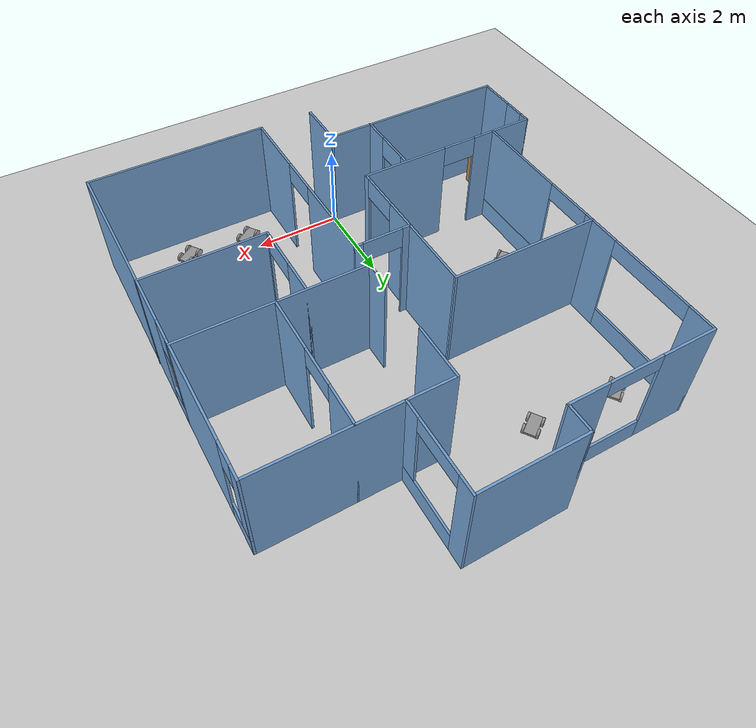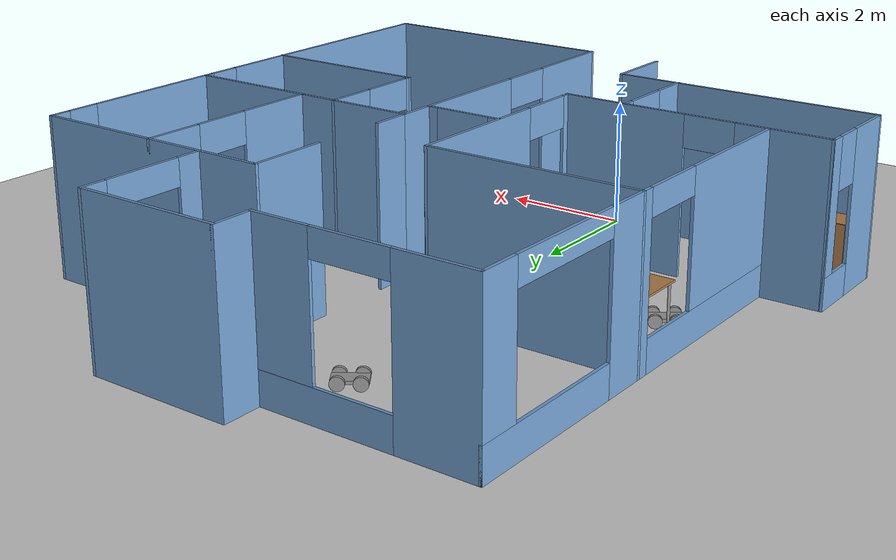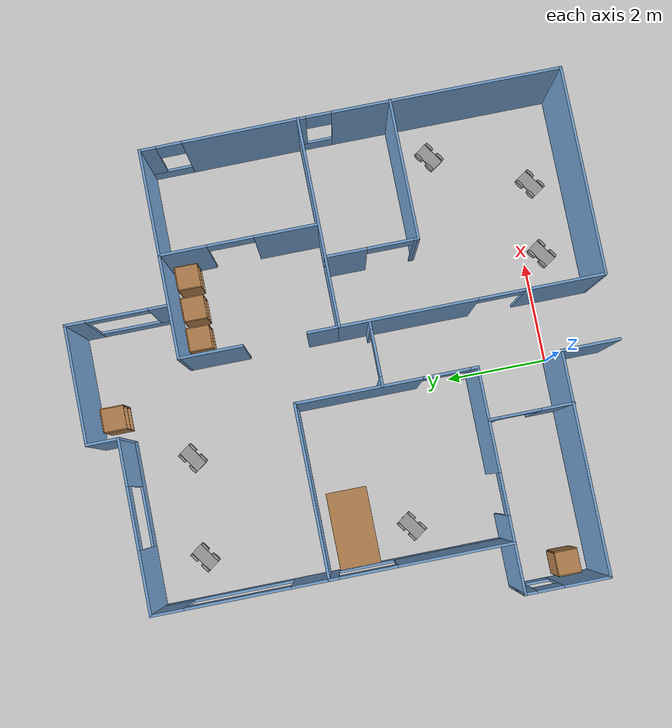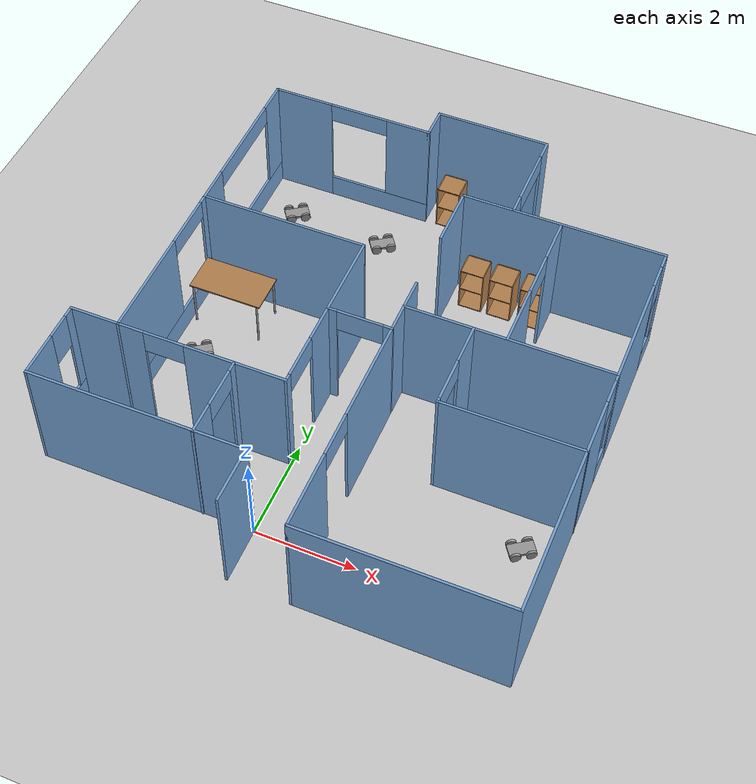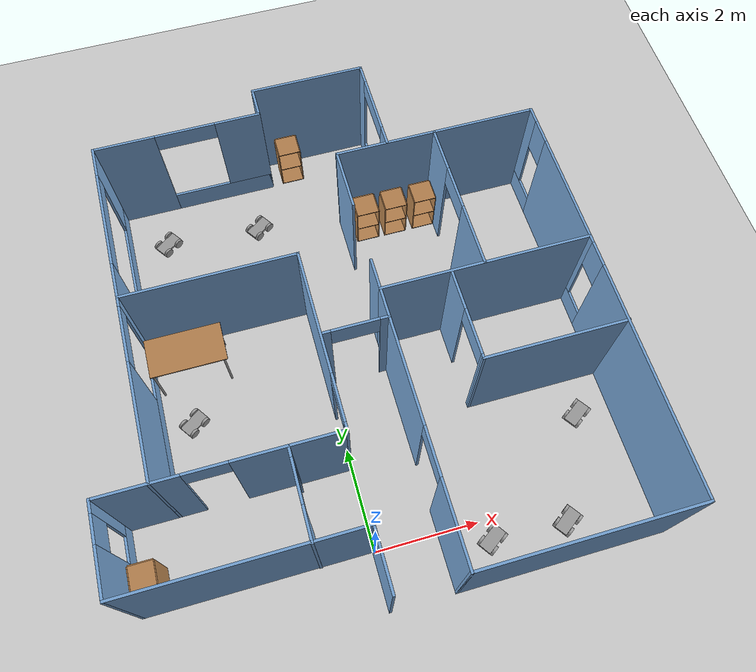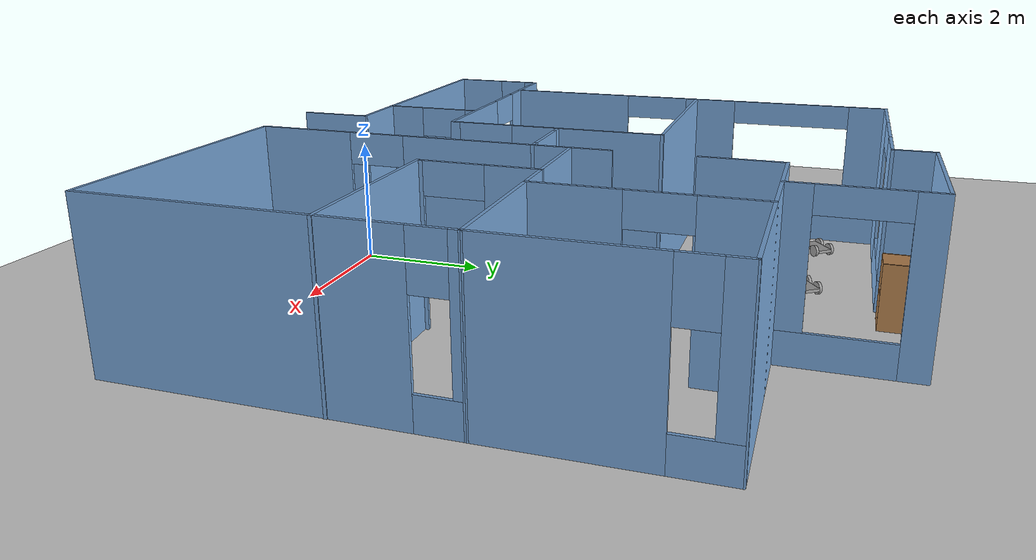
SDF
<sdf version="1.6">
 <world name="default">
  <light name="sun" type="directional">
   <pose>0 0 10 0 -0 0</pose>
   <diffuse>0.8 0.8 0.8 1</diffuse>
   <specular>0.2 0.2 0.2 1</specular>
   <attenuation>
    <range>1000</range>
    <constant>0.9</constant>
    <linear>0.01</linear>
    <quadratic>0.001</quadratic>
   </attenuation>
   <direction>-0.5 0.1 -0.9</direction>
  </light>
  <model name="ground_plane">
   <static>1</static>
   <link name="link">
    <collision name="collision">
     <geometry><plane><normal>0 0 1</normal><size>100 100</size></plane></geometry>
     <surface>
      <contact><collide_bitmask>65535</collide_bitmask></contact>
      <friction><ode><mu>100</mu><mu2>50</mu2></ode></friction>
     </surface>
    </collision>
    <visual name="visual">
     <cast_shadows>0</cast_shadows>
     <geometry><plane><normal>0 0 1</normal><size>100 100</size></plane></geometry>
     <material>
      <script><uri>file://media/materials/scripts/gazebo.material</uri><name>Gazebo/Grey</name></script>
     </material>
    </visual>
   </link>
  </model>
  <gravity>0 0 -9.8</gravity>
  <magnetic_field>6e-06 2.3e-05 -4.2e-05</magnetic_field>
  <atmosphere type="adiabatic"/>
  <physics name="default_physics" default="0" type="ode">
   <max_step_size>0.001</max_step_size>
   <real_time_factor>1</real_time_factor>
   <real_time_update_rate>1000</real_time_update_rate>
  </physics>
  <scene><ambient>0.4 0.4 0.4 1</ambient><background>0.7 0.7 0.7 1</background><shadows>1</shadows></scene>
  <audio><device>default</device></audio>
  <spherical_coordinates>
   <surface_model>EARTH_WGS84</surface_model>
   <latitude_deg>0</latitude_deg>
   <longitude_deg>0</longitude_deg>
   <elevation>0</elevation>
   <heading_deg>0</heading_deg>
  </spherical_coordinates>
  <model name="table">
   <static>1</static>
   <link name="link">
    <collision name="surface">
     <pose>0 0 1 0 -0 0</pose>
     <geometry><box><size>1.5 0.8 0.03</size></box></geometry>
     <surface><friction><ode><mu>0.6</mu><mu2>0.6</mu2></ode></friction></surface>
    </collision>
    <visual name="visual1">
     <pose>0 0 1 0 -0 0</pose>
     <geometry><box><size>1.5 0.8 0.03</size></box></geometry>
     <material>
      <script><uri>file://media/materials/scripts/gazebo.material</uri><name>Gazebo/Wood</name></script>
     </material>
    </visual>
    <collision name="front_left_leg">
     <pose>0.68 0.38 0.5 0 -0 0</pose>
     <geometry><cylinder><radius>0.02</radius><length>1</length></cylinder></geometry>
    </collision>
    <visual name="front_left_leg">
     <pose>0.68 0.38 0.5 0 -0 0</pose>
     <geometry><cylinder><radius>0.02</radius><length>1</length></cylinder></geometry>
     <material>
      <script><uri>file://media/materials/scripts/gazebo.material</uri><name>Gazebo/Grey</name></script>
     </material>
    </visual>
    <collision name="front_right_leg">
     <pose>0.68 -0.38 0.5 0 -0 0</pose>
     <geometry><cylinder><radius>0.02</radius><length>1</length></cylinder></geometry>
    </collision>
    <visual name="front_right_leg">
     <pose>0.68 -0.38 0.5 0 -0 0</pose>
     <geometry><cylinder><radius>0.02</radius><length>1</length></cylinder></geometry>
     <material>
      <script><uri>file://media/materials/scripts/gazebo.material</uri><name>Gazebo/Grey</name></script>
     </material>
    </visual>
    <collision name="back_right_leg">
     <pose>-0.68 -0.38 0.5 0 -0 0</pose>
     <geometry><cylinder><radius>0.02</radius><length>1</length></cylinder></geometry>
    </collision>
    <visual name="back_right_leg">
     <pose>-0.68 -0.38 0.5 0 -0 0</pose>
     <geometry><cylinder><radius>0.02</radius><length>1</length></cylinder></geometry>
     <material>
      <script><uri>file://media/materials/scripts/gazebo.material</uri><name>Gazebo/Grey</name></script>
     </material>
    </visual>
    <collision name="back_left_leg">
     <pose>-0.68 0.38 0.5 0 -0 0</pose>
     <geometry><cylinder><radius>0.02</radius><length>1</length></cylinder></geometry>
    </collision>
    <visual name="back_left_leg">
     <pose>-0.68 0.38 0.5 0 -0 0</pose>
     <geometry><cylinder><radius>0.02</radius><length>1</length></cylinder></geometry>
     <material>
      <script><uri>file://media/materials/scripts/gazebo.material</uri><name>Gazebo/Grey</name></script>
     </material>
    </visual>
   </link>
   <pose>-2.52101 4.48364 0 0 -0 0</pose>
  </model>
  <model name="cabinet">
   <static>1</static>
   <link name="cabinet_bottom_plate">
    <inertial>
     <pose>0 0 -1 0 -0 0</pose>
     <inertia><ixx>2.05</ixx><ixy>0</ixy><ixz>0</ixz><iyy>2.05</iyy><iyz>0</iyz><izz>2.05</izz></inertia>
     <mass>25</mass>
    </inertial>
    <collision name="cabinet_bottom_plate_geom">
     <pose>0 0 0.01 0 -0 0</pose>
     <geometry><box><size>0.45 0.45 0.02</size></box></geometry>
    </collision>
    <visual name="cabinet_bottom_plate_geom_visual">
     <pose>0 0 0.01 0 -0 0</pose>
     <geometry><box><size>0.45 0.45 0.02</size></box></geometry>
     <material>
      <script><uri>file://media/materials/scripts/gazebo.material</uri><name>Gazebo/Wood</name></script>
     </material>
    </visual>
    <collision name="cabinet_bottom_plate_geom_cabinet_back_plate">
     <pose>0.235 0 0.51 0 -0 0</pose>
     <geometry><box><size>0.02 0.45 1.02</size></box></geometry>
    </collision>
    <visual name="cabinet_bottom_plate_geom_cabinet_back_plate_visual">
     <pose>0.235 0 0.51 0 -0 0</pose>
     <geometry><box><size>0.02 0.45 1.02</size></box></geometry>
     <material>
      <script><uri>file://media/materials/scripts/gazebo.material</uri><name>Gazebo/Wood</name></script>
     </material>
    </visual>
    <collision name="cabinet_bottom_plate_geom_cabinet_left_plate">
     <pose>0 0.235 0.51 0 -0 0</pose>
     <geometry><box><size>0.45 0.02 1.02</size></box></geometry>
    </collision>
    <visual name="cabinet_bottom_plate_geom_cabinet_left_plate_visual">
     <pose>0 0.235 0.51 0 -0 0</pose>
     <geometry><box><size>0.45 0.02 1.02</size></box></geometry>
     <material>
      <script><uri>file://media/materials/scripts/gazebo.material</uri><name>Gazebo/Wood</name></script>
     </material>
    </visual>
    <collision name="cabinet_bottom_plate_geom_cabinet_middle_plate">
     <pose>0 0 0.51 0 -0 0</pose>
     <geometry><box><size>0.45 0.45 0.02</size></box></geometry>
    </collision>
    <visual name="cabinet_bottom_plate_geom_cabinet_middle_plate_visual">
     <pose>0 0 0.51 0 -0 0</pose>
     <geometry><box><size>0.45 0.45 0.02</size></box></geometry>
     <material>
      <script><uri>file://media/materials/scripts/gazebo.material</uri><name>Gazebo/Wood</name></script>
     </material>
    </visual>
    <collision name="cabinet_bottom_plate_geom_cabinet_right_plate">
     <pose>0 -0.235 0.51 0 -0 0</pose>
     <geometry><box><size>0.45 0.02 1.02</size></box></geometry>
    </collision>
    <visual name="cabinet_bottom_plate_geom_cabinet_right_plate_visual">
     <pose>0 -0.235 0.51 0 -0 0</pose>
     <geometry><box><size>0.45 0.02 1.02</size></box></geometry>
     <material>
      <script><uri>file://media/materials/scripts/gazebo.material</uri><name>Gazebo/Wood</name></script>
     </material>
    </visual>
    <collision name="cabinet_bottom_plate_geom_cabinet_top_plate">
     <pose>0 0 1.01 0 -0 0</pose>
     <geometry><box><size>0.45 0.45 0.02</size></box></geometry>
    </collision>
    <visual name="cabinet_bottom_plate_geom_cabinet_top_plate_visual">
     <pose>0 0 1.01 0 -0 0</pose>
     <geometry><box><size>0.45 0.45 0.02</size></box></geometry>
     <material>
      <script><uri>file://media/materials/scripts/gazebo.material</uri><name>Gazebo/Wood</name></script>
     </material>
    </visual>
   </link>
   <pose>2.94164 6.72302 0 0 -0 1.57</pose>
  </model>
  <model name="cabinet_clone">
   <static>1</static>
   <link name="cabinet_bottom_plate">
    <inertial>
     <pose>0 0 -1 0 -0 0</pose>
     <inertia><ixx>2.05</ixx><ixy>0</ixy><ixz>0</ixz><iyy>2.05</iyy><iyz>0</iyz><izz>2.05</izz></inertia>
     <mass>25</mass>
    </inertial>
    <collision name="cabinet_bottom_plate_geom">
     <pose>0 0 0.01 0 -0 0</pose>
     <geometry><box><size>0.45 0.45 0.02</size></box></geometry>
    </collision>
    <visual name="cabinet_bottom_plate_geom_visual">
     <pose>0 0 0.01 0 -0 0</pose>
     <geometry><box><size>0.45 0.45 0.02</size></box></geometry>
     <material>
      <script><uri>file://media/materials/scripts/gazebo.material</uri><name>Gazebo/Wood</name></script>
     </material>
    </visual>
    <collision name="cabinet_bottom_plate_geom_cabinet_back_plate">
     <pose>0.235 0 0.51 0 -0 0</pose>
     <geometry><box><size>0.02 0.45 1.02</size></box></geometry>
    </collision>
    <visual name="cabinet_bottom_plate_geom_cabinet_back_plate_visual">
     <pose>0.235 0 0.51 0 -0 0</pose>
     <geometry><box><size>0.02 0.45 1.02</size></box></geometry>
     <material>
      <script><uri>file://media/materials/scripts/gazebo.material</uri><name>Gazebo/Wood</name></script>
     </material>
    </visual>
    <collision name="cabinet_bottom_plate_geom_cabinet_left_plate">
     <pose>0 0.235 0.51 0 -0 0</pose>
     <geometry><box><size>0.45 0.02 1.02</size></box></geometry>
    </collision>
    <visual name="cabinet_bottom_plate_geom_cabinet_left_plate_visual">
     <pose>0 0.235 0.51 0 -0 0</pose>
     <geometry><box><size>0.45 0.02 1.02</size></box></geometry>
     <material>
      <script><uri>file://media/materials/scripts/gazebo.material</uri><name>Gazebo/Wood</name></script>
     </material>
    </visual>
    <collision name="cabinet_bottom_plate_geom_cabinet_middle_plate">
     <pose>0 0 0.51 0 -0 0</pose>
     <geometry><box><size>0.45 0.45 0.02</size></box></geometry>
    </collision>
    <visual name="cabinet_bottom_plate_geom_cabinet_middle_plate_visual">
     <pose>0 0 0.51 0 -0 0</pose>
     <geometry><box><size>0.45 0.45 0.02</size></box></geometry>
     <material>
      <script><uri>file://media/materials/scripts/gazebo.material</uri><name>Gazebo/Wood</name></script>
     </material>
    </visual>
    <collision name="cabinet_bottom_plate_geom_cabinet_right_plate">
     <pose>0 -0.235 0.51 0 -0 0</pose>
     <geometry><box><size>0.45 0.02 1.02</size></box></geometry>
    </collision>
    <visual name="cabinet_bottom_plate_geom_cabinet_right_plate_visual">
     <pose>0 -0.235 0.51 0 -0 0</pose>
     <geometry><box><size>0.45 0.02 1.02</size></box></geometry>
     <material>
      <script><uri>file://media/materials/scripts/gazebo.material</uri><name>Gazebo/Wood</name></script>
     </material>
    </visual>
    <collision name="cabinet_bottom_plate_geom_cabinet_top_plate">
     <pose>0 0 1.01 0 -0 0</pose>
     <geometry><box><size>0.45 0.45 0.02</size></box></geometry>
    </collision>
    <visual name="cabinet_bottom_plate_geom_cabinet_top_plate_visual">
     <pose>0 0 1.01 0 -0 0</pose>
     <geometry><box><size>0.45 0.45 0.02</size></box></geometry>
     <material>
      <script><uri>file://media/materials/scripts/gazebo.material</uri><name>Gazebo/Wood</name></script>
     </material>
    </visual>
   </link>
   <pose>2.30652 6.72096 0 0 -0 1.57</pose>
  </model>
  <model name="cabinet_clone_0">
   <static>1</static>
   <link name="cabinet_bottom_plate">
    <inertial>
     <pose>0 0 -1 0 -0 0</pose>
     <inertia><ixx>2.05</ixx><ixy>0</ixy><ixz>0</ixz><iyy>2.05</iyy><iyz>0</iyz><izz>2.05</izz></inertia>
     <mass>25</mass>
    </inertial>
    <collision name="cabinet_bottom_plate_geom">
     <pose>0 0 0.01 0 -0 0</pose>
     <geometry><box><size>0.45 0.45 0.02</size></box></geometry>
    </collision>
    <visual name="cabinet_bottom_plate_geom_visual">
     <pose>0 0 0.01 0 -0 0</pose>
     <geometry><box><size>0.45 0.45 0.02</size></box></geometry>
     <material>
      <script><uri>file://media/materials/scripts/gazebo.material</uri><name>Gazebo/Wood</name></script>
     </material>
    </visual>
    <collision name="cabinet_bottom_plate_geom_cabinet_back_plate">
     <pose>0.235 0 0.51 0 -0 0</pose>
     <geometry><box><size>0.02 0.45 1.02</size></box></geometry>
    </collision>
    <visual name="cabinet_bottom_plate_geom_cabinet_back_plate_visual">
     <pose>0.235 0 0.51 0 -0 0</pose>
     <geometry><box><size>0.02 0.45 1.02</size></box></geometry>
     <material>
      <script><uri>file://media/materials/scripts/gazebo.material</uri><name>Gazebo/Wood</name></script>
     </material>
    </visual>
    <collision name="cabinet_bottom_plate_geom_cabinet_left_plate">
     <pose>0 0.235 0.51 0 -0 0</pose>
     <geometry><box><size>0.45 0.02 1.02</size></box></geometry>
    </collision>
    <visual name="cabinet_bottom_plate_geom_cabinet_left_plate_visual">
     <pose>0 0.235 0.51 0 -0 0</pose>
     <geometry><box><size>0.45 0.02 1.02</size></box></geometry>
     <material>
      <script><uri>file://media/materials/scripts/gazebo.material</uri><name>Gazebo/Wood</name></script>
     </material>
    </visual>
    <collision name="cabinet_bottom_plate_geom_cabinet_middle_plate">
     <pose>0 0 0.51 0 -0 0</pose>
     <geometry><box><size>0.45 0.45 0.02</size></box></geometry>
    </collision>
    <visual name="cabinet_bottom_plate_geom_cabinet_middle_plate_visual">
     <pose>0 0 0.51 0 -0 0</pose>
     <geometry><box><size>0.45 0.45 0.02</size></box></geometry>
     <material>
      <script><uri>file://media/materials/scripts/gazebo.material</uri><name>Gazebo/Wood</name></script>
     </material>
    </visual>
    <collision name="cabinet_bottom_plate_geom_cabinet_right_plate">
     <pose>0 -0.235 0.51 0 -0 0</pose>
     <geometry><box><size>0.45 0.02 1.02</size></box></geometry>
    </collision>
    <visual name="cabinet_bottom_plate_geom_cabinet_right_plate_visual">
     <pose>0 -0.235 0.51 0 -0 0</pose>
     <geometry><box><size>0.45 0.02 1.02</size></box></geometry>
     <material>
      <script><uri>file://media/materials/scripts/gazebo.material</uri><name>Gazebo/Wood</name></script>
     </material>
    </visual>
    <collision name="cabinet_bottom_plate_geom_cabinet_top_plate">
     <pose>0 0 1.01 0 -0 0</pose>
     <geometry><box><size>0.45 0.45 0.02</size></box></geometry>
    </collision>
    <visual name="cabinet_bottom_plate_geom_cabinet_top_plate_visual">
     <pose>0 0 1.01 0 -0 0</pose>
     <geometry><box><size>0.45 0.45 0.02</size></box></geometry>
     <material>
      <script><uri>file://media/materials/scripts/gazebo.material</uri><name>Gazebo/Wood</name></script>
     </material>
    </visual>
   </link>
   <pose>1.70059 6.72405 0 0 -0 1.57</pose>
  </model>
  <model name="T8_1160">
   <pose>0.49359 3.97815 0 0 -0 0</pose>
   <link name="Wall_0">
    <collision name="Wall_0_Collision">
     <geometry><box><size>4.31 0.05 2.5</size></box></geometry>
     <pose>0 0 1.25 0 -0 0</pose>
    </collision>
    <visual name="Wall_0_Visual">
     <pose>0 0 1.25 0 -0 0</pose>
     <geometry><box><size>4.31 0.05 2.5</size></box></geometry>
     <material>
      <script><uri>file://media/materials/scripts/gazebo.material</uri><name>Gazebo/Grey</name></script>
      <ambient>0.447059 0.623529 0.811765 1</ambient>
     </material>
     <meta><layer>0</layer></meta>
    </visual>
    <pose>-2.645 -3.94713 0 0 -0 3.14159</pose>
   </link>
   <link name="Wall_11">
    <collision name="Wall_11_Collision">
     <geometry><box><size>3.35552 0.05 2.5</size></box></geometry>
     <pose>0 0 1.25 0 -0 0</pose>
    </collision>
    <visual name="Wall_11_Visual">
     <pose>0 0 1.25 0 -0 0</pose>
     <geometry><box><size>3.35552 0.05 2.5</size></box></geometry>
     <material>
      <script><uri>file://media/materials/scripts/gazebo.material</uri><name>Gazebo/Grey</name></script>
      <ambient>0.447059 0.623529 0.811765 1</ambient>
     </material>
     <meta><layer>0</layer></meta>
    </visual>
    <pose>-2.1675 1.12987 0 0 -0 3.14159</pose>
   </link>
   <link name="Wall_14">
    <pose>-3.82 -0.608633 0 0 -0 -1.5708</pose>
    <visual name="Wall_14_Visual_0">
     <pose>-1.65666 0 1.25 0 -0 0</pose>
     <geometry><box><size>0.213672 0.05 2.5</size></box></geometry>
     <material>
      <script><uri>file://media/materials/scripts/gazebo.material</uri><name>Gazebo/Grey</name></script>
      <ambient>0.447059 0.623529 0.811765 1</ambient>
     </material>
     <meta><layer>0</layer></meta>
    </visual>
    <collision name="Wall_14_Collision_0">
     <geometry><box><size>0.213672 0.05 2.5</size></box></geometry>
     <pose>-1.65666 0 1.25 0 -0 0</pose>
    </collision>
    <visual name="Wall_14_Visual_1">
     <pose>0.106836 0 0.25 0 -0 0</pose>
     <geometry><box><size>3.31333 0.05 0.5</size></box></geometry>
     <material>
      <script><uri>file://media/materials/scripts/gazebo.material</uri><name>Gazebo/Grey</name></script>
      <ambient>0.447059 0.623529 0.811765 1</ambient>
     </material>
     <meta><layer>0</layer></meta>
    </visual>
    <collision name="Wall_14_Collision_1">
     <geometry><box><size>3.31333 0.05 0.5</size></box></geometry>
     <pose>0.106836 0 0.25 0 -0 0</pose>
    </collision>
    <visual name="Wall_14_Visual_2">
     <pose>0.656836 0 1.5 0 -0 0</pose>
     <geometry><box><size>2.21333 0.05 2</size></box></geometry>
     <material>
      <script><uri>file://media/materials/scripts/gazebo.material</uri><name>Gazebo/Grey</name></script>
      <ambient>0.447059 0.623529 0.811765 1</ambient>
     </material>
     <meta><layer>0</layer></meta>
    </visual>
    <collision name="Wall_14_Collision_2">
     <geometry><box><size>2.21333 0.05 2</size></box></geometry>
     <pose>0.656836 0 1.5 0 -0 0</pose>
    </collision>
    <visual name="Wall_14_Visual_3">
     <pose>-0.999828 0 2.3 0 -0 0</pose>
     <geometry><box><size>1.1 0.05 0.4</size></box></geometry>
     <material>
      <script><uri>file://media/materials/scripts/gazebo.material</uri><name>Gazebo/Grey</name></script>
      <ambient>0.447059 0.623529 0.811765 1</ambient>
     </material>
     <meta><layer>0</layer></meta>
    </visual>
    <collision name="Wall_14_Collision_3">
     <geometry><box><size>1.1 0.05 0.4</size></box></geometry>
     <pose>-0.999828 0 2.3 0 -0 0</pose>
    </collision>
   </link>
   <link name="Wall_16">
    <collision name="Wall_16_Collision">
     <geometry><box><size>1.15 0.05 2.5</size></box></geometry>
     <pose>0 0 1.25 0 -0 0</pose>
    </collision>
    <visual name="Wall_16_Visual">
     <pose>0 0 1.25 0 -0 0</pose>
     <geometry><box><size>1.15 0.05 2.5</size></box></geometry>
     <material>
      <script><uri>file://media/materials/scripts/gazebo.material</uri><name>Gazebo/Grey</name></script>
      <ambient>0.447059 0.623529 0.811765 1</ambient>
     </material>
     <meta><layer>0</layer></meta>
    </visual>
    <pose>-0.515 -4.49713 0 0 -0 -1.5708</pose>
   </link>
   <link name="Wall_18">
    <pose>0.735 -2.51163 0 0 -0 1.5708</pose>
    <visual name="Wall_18_Visual_0">
     <pose>-1.78983 0 1.25 0 -0 0</pose>
     <geometry><box><size>1.56134 0.05 2.5</size></box></geometry>
     <material>
      <script><uri>file://media/materials/scripts/gazebo.material</uri><name>Gazebo/Grey</name></script>
      <ambient>0.447059 0.623529 0.811765 1</ambient>
     </material>
     <meta><layer>0</layer></meta>
    </visual>
    <collision name="Wall_18_Collision_0">
     <geometry><box><size>1.56134 0.05 2.5</size></box></geometry>
     <pose>-1.78983 0 1.25 0 -0 0</pose>
    </collision>
    <visual name="Wall_18_Visual_1">
     <pose>1.23067 0 1.25 0 -0 0</pose>
     <geometry><box><size>2.67966 0.05 2.5</size></box></geometry>
     <material>
      <script><uri>file://media/materials/scripts/gazebo.material</uri><name>Gazebo/Grey</name></script>
      <ambient>0.447059 0.623529 0.811765 1</ambient>
     </material>
     <meta><layer>0</layer></meta>
    </visual>
    <collision name="Wall_18_Collision_1">
     <geometry><box><size>2.67966 0.05 2.5</size></box></geometry>
     <pose>1.23067 0 1.25 0 -0 0</pose>
    </collision>
    <visual name="Wall_18_Visual_2">
     <pose>-0.559159 0 2.25 0 -0 0</pose>
     <geometry><box><size>0.9 0.05 0.5</size></box></geometry>
     <material>
      <script><uri>file://media/materials/scripts/gazebo.material</uri><name>Gazebo/Grey</name></script>
      <ambient>0.447059 0.623529 0.811765 1</ambient>
     </material>
     <meta><layer>0</layer></meta>
    </visual>
    <collision name="Wall_18_Collision_2">
     <geometry><box><size>0.9 0.05 0.5</size></box></geometry>
     <pose>-0.559159 0 2.25 0 -0 0</pose>
    </collision>
   </link>
   <link name="Wall_2">
    <pose>-4.775 -3.14713 0 0 -0 1.5708</pose>
    <visual name="Wall_2_Visual_0">
     <pose>-0.375725 0 1.25 0 -0 0</pose>
     <geometry><box><size>0.89855 0.05 2.5</size></box></geometry>
     <material>
      <script><uri>file://media/materials/scripts/gazebo.material</uri><name>Gazebo/Grey</name></script>
      <ambient>0.447059 0.623529 0.811765 1</ambient>
     </material>
     <meta><layer>0</layer></meta>
    </visual>
    <collision name="Wall_2_Collision_0">
     <geometry><box><size>0.89855 0.05 2.5</size></box></geometry>
     <pose>-0.375725 0 1.25 0 -0 0</pose>
    </collision>
    <visual name="Wall_2_Visual_1">
     <pose>0.449275 0 0.25 0 -0 0</pose>
     <geometry><box><size>0.75145 0.05 0.5</size></box></geometry>
     <material>
      <script><uri>file://media/materials/scripts/gazebo.material</uri><name>Gazebo/Grey</name></script>
      <ambient>0.447059 0.623529 0.811765 1</ambient>
     </material>
     <meta><layer>0</layer></meta>
    </visual>
    <collision name="Wall_2_Collision_1">
     <geometry><box><size>0.75145 0.05 0.5</size></box></geometry>
     <pose>0.449275 0 0.25 0 -0 0</pose>
    </collision>
    <visual name="Wall_2_Visual_2">
     <pose>0.699275 0 1.5 0 -0 0</pose>
     <geometry><box><size>0.25145 0.05 2</size></box></geometry>
     <material>
      <script><uri>file://media/materials/scripts/gazebo.material</uri><name>Gazebo/Grey</name></script>
      <ambient>0.447059 0.623529 0.811765 1</ambient>
     </material>
     <meta><layer>0</layer></meta>
    </visual>
    <collision name="Wall_2_Collision_2">
     <geometry><box><size>0.25145 0.05 2</size></box></geometry>
     <pose>0.699275 0 1.5 0 -0 0</pose>
    </collision>
    <visual name="Wall_2_Visual_3">
     <pose>0.32355 0 2.1 0 -0 0</pose>
     <geometry><box><size>0.5 0.05 0.8</size></box></geometry>
     <material>
      <script><uri>file://media/materials/scripts/gazebo.material</uri><name>Gazebo/Grey</name></script>
      <ambient>0.447059 0.623529 0.811765 1</ambient>
     </material>
     <meta><layer>0</layer></meta>
    </visual>
    <collision name="Wall_2_Collision_3">
     <geometry><box><size>0.5 0.05 0.8</size></box></geometry>
     <pose>0.32355 0 2.1 0 -0 0</pose>
    </collision>
   </link>
   <link name="Wall_20">
    <collision name="Wall_20_Collision">
     <geometry><box><size>4.08 0.05 2.5</size></box></geometry>
     <pose>0 0 1.25 0 -0 0</pose>
    </collision>
    <visual name="Wall_20_Visual">
     <pose>0 0 1.25 0 -0 0</pose>
     <geometry><box><size>4.08 0.05 2.5</size></box></geometry>
     <material>
      <script><uri>file://media/materials/scripts/gazebo.material</uri><name>Gazebo/Grey</name></script>
      <ambient>0.447059 0.623529 0.811765 1</ambient>
     </material>
     <meta><layer>0</layer></meta>
    </visual>
    <pose>2.75 -5.05713 0 0 -0 0</pose>
   </link>
   <link name="Wall_22">
    <pose>4.765 -2.51163 0 0 -0 1.5708</pose>
    <visual name="Wall_22_Visual_0">
     <pose>-0.335589 0 1.25 0 -0 0</pose>
     <geometry><box><size>4.46982 0.05 2.5</size></box></geometry>
     <material>
      <script><uri>file://media/materials/scripts/gazebo.material</uri><name>Gazebo/Grey</name></script>
      <ambient>0.447059 0.623529 0.811765 1</ambient>
     </material>
     <meta><layer>0</layer></meta>
    </visual>
    <collision name="Wall_22_Collision_0">
     <geometry><box><size>4.46982 0.05 2.5</size></box></geometry>
     <pose>-0.335589 0 1.25 0 -0 0</pose>
    </collision>
    <visual name="Wall_22_Visual_1">
     <pose>2.23491 0 0.25 0 -0 0</pose>
     <geometry><box><size>0.671178 0.05 0.5</size></box></geometry>
     <material>
      <script><uri>file://media/materials/scripts/gazebo.material</uri><name>Gazebo/Grey</name></script>
      <ambient>0.447059 0.623529 0.811765 1</ambient>
     </material>
     <meta><layer>0</layer></meta>
    </visual>
    <collision name="Wall_22_Collision_1">
     <geometry><box><size>0.671178 0.05 0.5</size></box></geometry>
     <pose>2.23491 0 0.25 0 -0 0</pose>
    </collision>
    <visual name="Wall_22_Visual_2">
     <pose>2.48491 0 1.5 0 -0 0</pose>
     <geometry><box><size>0.171178 0.05 2</size></box></geometry>
     <material>
      <script><uri>file://media/materials/scripts/gazebo.material</uri><name>Gazebo/Grey</name></script>
      <ambient>0.447059 0.623529 0.811765 1</ambient>
     </material>
     <meta><layer>0</layer></meta>
    </visual>
    <collision name="Wall_22_Collision_2">
     <geometry><box><size>0.171178 0.05 2</size></box></geometry>
     <pose>2.48491 0 1.5 0 -0 0</pose>
    </collision>
    <visual name="Wall_22_Visual_3">
     <pose>2.14932 0 2.1 0 -0 0</pose>
     <geometry><box><size>0.5 0.05 0.8</size></box></geometry>
     <material>
      <script><uri>file://media/materials/scripts/gazebo.material</uri><name>Gazebo/Grey</name></script>
      <ambient>0.447059 0.623529 0.811765 1</ambient>
     </material>
     <meta><layer>0</layer></meta>
    </visual>
    <collision name="Wall_22_Collision_3">
     <geometry><box><size>0.5 0.05 0.8</size></box></geometry>
     <pose>2.14932 0 2.1 0 -0 0</pose>
    </collision>
   </link>
   <link name="Wall_24">
    <collision name="Wall_24_Collision">
     <geometry><box><size>4.08 0.05 2.5</size></box></geometry>
     <pose>0 0 1.25 0 -0 0</pose>
    </collision>
    <visual name="Wall_24_Visual">
     <pose>0 0 1.25 0 -0 0</pose>
     <geometry><box><size>4.08 0.05 2.5</size></box></geometry>
     <material>
      <script><uri>file://media/materials/scripts/gazebo.material</uri><name>Gazebo/Grey</name></script>
      <ambient>0.447059 0.623529 0.811765 1</ambient>
     </material>
     <meta><layer>0</layer></meta>
    </visual>
    <pose>2.75 0.033867 0 0 -0 0</pose>
   </link>
   <link name="Wall_27">
    <pose>0.1145 -0.539133 0 0 -0 0</pose>
    <visual name="Wall_27_Visual_0">
     <pose>-0.547154 0 1.25 0 -0 0</pose>
     <geometry><box><size>0.196693 0.05 2.5</size></box></geometry>
     <material>
      <script><uri>file://media/materials/scripts/gazebo.material</uri><name>Gazebo/Grey</name></script>
      <ambient>0.447059 0.623529 0.811765 1</ambient>
     </material>
     <meta><layer>0</layer></meta>
    </visual>
    <collision name="Wall_27_Collision_0">
     <geometry><box><size>0.196693 0.05 2.5</size></box></geometry>
     <pose>-0.547154 0 1.25 0 -0 0</pose>
    </collision>
    <visual name="Wall_27_Visual_1">
     <pose>0.548346 0 1.25 0 -0 0</pose>
     <geometry><box><size>0.194307 0.05 2.5</size></box></geometry>
     <material>
      <script><uri>file://media/materials/scripts/gazebo.material</uri><name>Gazebo/Grey</name></script>
      <ambient>0.447059 0.623529 0.811765 1</ambient>
     </material>
     <meta><layer>0</layer></meta>
    </visual>
    <collision name="Wall_27_Collision_1">
     <geometry><box><size>0.194307 0.05 2.5</size></box></geometry>
     <pose>0.548346 0 1.25 0 -0 0</pose>
    </collision>
    <visual name="Wall_27_Visual_2">
     <pose>0.001193 0 2.25 0 -0 0</pose>
     <geometry><box><size>0.9 0.05 0.5</size></box></geometry>
     <material>
      <script><uri>file://media/materials/scripts/gazebo.material</uri><name>Gazebo/Grey</name></script>
      <ambient>0.447059 0.623529 0.811765 1</ambient>
     </material>
     <meta><layer>0</layer></meta>
    </visual>
    <collision name="Wall_27_Collision_2">
     <geometry><box><size>0.9 0.05 0.5</size></box></geometry>
     <pose>0.001193 0 2.25 0 -0 0</pose>
    </collision>
   </link>
   <link name="Wall_29">
    <collision name="Wall_29_Collision">
     <geometry><box><size>0.65 0.05 2.5</size></box></geometry>
     <pose>0 0 1.25 0 -0 0</pose>
    </collision>
    <visual name="Wall_29_Visual">
     <pose>0 0 1.25 0 -0 0</pose>
     <geometry><box><size>0.65 0.05 2.5</size></box></geometry>
     <material>
      <script><uri>file://media/materials/scripts/gazebo.material</uri><name>Gazebo/Grey</name></script>
      <ambient>0.447059 0.623529 0.811765 1</ambient>
     </material>
     <meta><layer>0</layer></meta>
    </visual>
    <pose>0.735 0.333867 0 0 -0 1.5708</pose>
   </link>
   <link name="Wall_31">
    <collision name="Wall_31_Collision">
     <geometry><box><size>2.75 0.05 2.5</size></box></geometry>
     <pose>0 0 1.25 0 -0 0</pose>
    </collision>
    <visual name="Wall_31_Visual">
     <pose>0 0 1.25 0 -0 0</pose>
     <geometry><box><size>2.75 0.05 2.5</size></box></geometry>
     <material>
      <script><uri>file://media/materials/scripts/gazebo.material</uri><name>Gazebo/Grey</name></script>
      <ambient>0.447059 0.623529 0.811765 1</ambient>
     </material>
     <meta><layer>0</layer></meta>
    </visual>
    <pose>3.425 -1.74713 0 0 -0 3.14159</pose>
   </link>
   <link name="Wall_33">
    <pose>2.075 -0.856633 0 0 -0 1.5708</pose>
    <visual name="Wall_33_Visual_0">
     <pose>-0.861434 0 1.25 0 -0 0</pose>
     <geometry><box><size>0.108132 0.05 2.5</size></box></geometry>
     <material>
      <script><uri>file://media/materials/scripts/gazebo.material</uri><name>Gazebo/Grey</name></script>
      <ambient>0.447059 0.623529 0.811765 1</ambient>
     </material>
     <meta><layer>0</layer></meta>
    </visual>
    <collision name="Wall_33_Collision_0">
     <geometry><box><size>0.108132 0.05 2.5</size></box></geometry>
     <pose>-0.861434 0 1.25 0 -0 0</pose>
    </collision>
    <visual name="Wall_33_Visual_1">
     <pose>0.504066 0 1.25 0 -0 0</pose>
     <geometry><box><size>0.822868 0.05 2.5</size></box></geometry>
     <material>
      <script><uri>file://media/materials/scripts/gazebo.material</uri><name>Gazebo/Grey</name></script>
      <ambient>0.447059 0.623529 0.811765 1</ambient>
     </material>
     <meta><layer>0</layer></meta>
    </visual>
    <collision name="Wall_33_Collision_1">
     <geometry><box><size>0.822868 0.05 2.5</size></box></geometry>
     <pose>0.504066 0 1.25 0 -0 0</pose>
    </collision>
    <visual name="Wall_33_Visual_2">
     <pose>-0.357368 0 2.25 0 -0 0</pose>
     <geometry><box><size>0.9 0.05 0.5</size></box></geometry>
     <material>
      <script><uri>file://media/materials/scripts/gazebo.material</uri><name>Gazebo/Grey</name></script>
      <ambient>0.447059 0.623529 0.811765 1</ambient>
     </material>
     <meta><layer>0</layer></meta>
    </visual>
    <collision name="Wall_33_Collision_2">
     <geometry><box><size>0.9 0.05 0.5</size></box></geometry>
     <pose>-0.357368 0 2.25 0 -0 0</pose>
    </collision>
   </link>
   <link name="Wall_35">
    <pose>-3.82 2.79337 0 0 -0 1.5708</pose>
    <visual name="Wall_35_Visual_0">
     <pose>-1.32132 0 1.25 0 -0 0</pose>
     <geometry><box><size>0.734362 0.05 2.5</size></box></geometry>
     <material>
      <script><uri>file://media/materials/scripts/gazebo.material</uri><name>Gazebo/Grey</name></script>
      <ambient>0.447059 0.623529 0.811765 1</ambient>
     </material>
     <meta><layer>0</layer></meta>
    </visual>
    <collision name="Wall_35_Collision_0">
     <geometry><box><size>0.734362 0.05 2.5</size></box></geometry>
     <pose>-1.32132 0 1.25 0 -0 0</pose>
    </collision>
    <visual name="Wall_35_Visual_1">
     <pose>0.367181 0 0.25 0 -0 0</pose>
     <geometry><box><size>2.64264 0.05 0.5</size></box></geometry>
     <material>
      <script><uri>file://media/materials/scripts/gazebo.material</uri><name>Gazebo/Grey</name></script>
      <ambient>0.447059 0.623529 0.811765 1</ambient>
     </material>
     <meta><layer>0</layer></meta>
    </visual>
    <collision name="Wall_35_Collision_1">
     <geometry><box><size>2.64264 0.05 0.5</size></box></geometry>
     <pose>0.367181 0 0.25 0 -0 0</pose>
    </collision>
    <visual name="Wall_35_Visual_2">
     <pose>1.36718 0 1.5 0 -0 0</pose>
     <geometry><box><size>0.642638 0.05 2</size></box></geometry>
     <material>
      <script><uri>file://media/materials/scripts/gazebo.material</uri><name>Gazebo/Grey</name></script>
      <ambient>0.447059 0.623529 0.811765 1</ambient>
     </material>
     <meta><layer>0</layer></meta>
    </visual>
    <collision name="Wall_35_Collision_2">
     <geometry><box><size>0.642638 0.05 2</size></box></geometry>
     <pose>1.36718 0 1.5 0 -0 0</pose>
    </collision>
    <visual name="Wall_35_Visual_3">
     <pose>0.045862 0 2.3 0 -0 0</pose>
     <geometry><box><size>2 0.05 0.4</size></box></geometry>
     <material>
      <script><uri>file://media/materials/scripts/gazebo.material</uri><name>Gazebo/Grey</name></script>
      <ambient>0.447059 0.623529 0.811765 1</ambient>
     </material>
     <meta><layer>0</layer></meta>
    </visual>
    <collision name="Wall_35_Collision_3">
     <geometry><box><size>2 0.05 0.4</size></box></geometry>
     <pose>0.045862 0 2.3 0 -0 0</pose>
    </collision>
   </link>
   <link name="Wall_37">
    <pose>-2.1675 4.45687 0 0 -0 0</pose>
    <visual name="Wall_37_Visual_0">
     <pose>-1.06148 0 1.25 0 -0 0</pose>
     <geometry><box><size>1.23203 0.05 2.5</size></box></geometry>
     <material>
      <script><uri>file://media/materials/scripts/gazebo.material</uri><name>Gazebo/Grey</name></script>
      <ambient>0.447059 0.623529 0.811765 1</ambient>
     </material>
     <meta><layer>0</layer></meta>
    </visual>
    <collision name="Wall_37_Collision_0">
     <geometry><box><size>1.23203 0.05 2.5</size></box></geometry>
     <pose>-1.06148 0 1.25 0 -0 0</pose>
    </collision>
    <visual name="Wall_37_Visual_1">
     <pose>0.616016 0 0.25 0 -0 0</pose>
     <geometry><box><size>2.12297 0.05 0.5</size></box></geometry>
     <material>
      <script><uri>file://media/materials/scripts/gazebo.material</uri><name>Gazebo/Grey</name></script>
      <ambient>0.447059 0.623529 0.811765 1</ambient>
     </material>
     <meta><layer>0</layer></meta>
    </visual>
    <collision name="Wall_37_Collision_1">
     <geometry><box><size>2.12297 0.05 0.5</size></box></geometry>
     <pose>0.616016 0 0.25 0 -0 0</pose>
    </collision>
    <visual name="Wall_37_Visual_2">
     <pose>1.21602 0 1.5 0 -0 0</pose>
     <geometry><box><size>0.922968 0.05 2</size></box></geometry>
     <material>
      <script><uri>file://media/materials/scripts/gazebo.material</uri><name>Gazebo/Grey</name></script>
      <ambient>0.447059 0.623529 0.811765 1</ambient>
     </material>
     <meta><layer>0</layer></meta>
    </visual>
    <collision name="Wall_37_Collision_2">
     <geometry><box><size>0.922968 0.05 2</size></box></geometry>
     <pose>1.21602 0 1.5 0 -0 0</pose>
    </collision>
    <visual name="Wall_37_Visual_3">
     <pose>0.154532 0 2.3 0 -0 0</pose>
     <geometry><box><size>1.2 0.05 0.4</size></box></geometry>
     <material>
      <script><uri>file://media/materials/scripts/gazebo.material</uri><name>Gazebo/Grey</name></script>
      <ambient>0.447059 0.623529 0.811765 1</ambient>
     </material>
     <meta><layer>0</layer></meta>
    </visual>
    <collision name="Wall_37_Collision_3">
     <geometry><box><size>1.2 0.05 0.4</size></box></geometry>
     <pose>0.154532 0 2.3 0 -0 0</pose>
    </collision>
   </link>
   <link name="Wall_39">
    <pose>4.755 1.56037 0 0 -0 1.57735</pose>
    <visual name="Wall_39_Visual_0">
     <pose>-0.419155 0 1.25 0 -0 0</pose>
     <geometry><box><size>2.26536 0.05 2.5</size></box></geometry>
     <material>
      <script><uri>file://media/materials/scripts/gazebo.material</uri><name>Gazebo/Grey</name></script>
      <ambient>0.447059 0.623529 0.811765 1</ambient>
     </material>
     <meta><layer>0</layer></meta>
    </visual>
    <collision name="Wall_39_Collision_0">
     <geometry><box><size>2.26536 0.05 2.5</size></box></geometry>
     <pose>-0.419155 0 1.25 0 -0 0</pose>
    </collision>
    <visual name="Wall_39_Visual_1">
     <pose>1.13268 0 0.25 0 -0 0</pose>
     <geometry><box><size>0.838311 0.05 0.5</size></box></geometry>
     <material>
      <script><uri>file://media/materials/scripts/gazebo.material</uri><name>Gazebo/Grey</name></script>
      <ambient>0.447059 0.623529 0.811765 1</ambient>
     </material>
     <meta><layer>0</layer></meta>
    </visual>
    <collision name="Wall_39_Collision_1">
     <geometry><box><size>0.838311 0.05 0.5</size></box></geometry>
     <pose>1.13268 0 0.25 0 -0 0</pose>
    </collision>
    <visual name="Wall_39_Visual_2">
     <pose>1.38268 0 1.5 0 -0 0</pose>
     <geometry><box><size>0.338311 0.05 2</size></box></geometry>
     <material>
      <script><uri>file://media/materials/scripts/gazebo.material</uri><name>Gazebo/Grey</name></script>
      <ambient>0.447059 0.623529 0.811765 1</ambient>
     </material>
     <meta><layer>0</layer></meta>
    </visual>
    <collision name="Wall_39_Collision_2">
     <geometry><box><size>0.338311 0.05 2</size></box></geometry>
     <pose>1.38268 0 1.5 0 -0 0</pose>
    </collision>
    <visual name="Wall_39_Visual_3">
     <pose>0.963525 0 2.1 0 -0 0</pose>
     <geometry><box><size>0.5 0.05 0.8</size></box></geometry>
     <material>
      <script><uri>file://media/materials/scripts/gazebo.material</uri><name>Gazebo/Grey</name></script>
      <ambient>0.447059 0.623529 0.811765 1</ambient>
     </material>
     <meta><layer>0</layer></meta>
    </visual>
    <collision name="Wall_39_Collision_3">
     <geometry><box><size>0.5 0.05 0.8</size></box></geometry>
     <pose>0.963525 0 2.1 0 -0 0</pose>
    </collision>
   </link>
   <link name="Wall_4">
    <pose>-2.645 -2.34713 0 0 -0 0</pose>
    <visual name="Wall_4_Visual_0">
     <pose>-1.40931 0 1.25 0 -0 0</pose>
     <geometry><box><size>1.49138 0.05 2.5</size></box></geometry>
     <material>
      <script><uri>file://media/materials/scripts/gazebo.material</uri><name>Gazebo/Grey</name></script>
      <ambient>0.447059 0.623529 0.811765 1</ambient>
     </material>
     <meta><layer>0</layer></meta>
    </visual>
    <collision name="Wall_4_Collision_0">
     <geometry><box><size>1.49138 0.05 2.5</size></box></geometry>
     <pose>-1.40931 0 1.25 0 -0 0</pose>
    </collision>
    <visual name="Wall_4_Visual_1">
     <pose>1.14569 0 1.25 0 -0 0</pose>
     <geometry><box><size>2.01862 0.05 2.5</size></box></geometry>
     <material>
      <script><uri>file://media/materials/scripts/gazebo.material</uri><name>Gazebo/Grey</name></script>
      <ambient>0.447059 0.623529 0.811765 1</ambient>
     </material>
     <meta><layer>0</layer></meta>
    </visual>
    <collision name="Wall_4_Collision_1">
     <geometry><box><size>2.01862 0.05 2.5</size></box></geometry>
     <pose>1.14569 0 1.25 0 -0 0</pose>
    </collision>
    <visual name="Wall_4_Visual_2">
     <pose>-0.263615 0 2.25 0 -0 0</pose>
     <geometry><box><size>0.8 0.05 0.5</size></box></geometry>
     <material>
      <script><uri>file://media/materials/scripts/gazebo.material</uri><name>Gazebo/Grey</name></script>
      <ambient>0.447059 0.623529 0.811765 1</ambient>
     </material>
     <meta><layer>0</layer></meta>
    </visual>
    <collision name="Wall_4_Collision_2">
     <geometry><box><size>0.8 0.05 0.5</size></box></geometry>
     <pose>-0.263615 0 2.25 0 -0 0</pose>
    </collision>
   </link>
   <link name="Wall_41">
    <collision name="Wall_41_Collision">
     <geometry><box><size>4.06 0.05 2.5</size></box></geometry>
     <pose>0 0 1.25 0 -0 0</pose>
    </collision>
    <visual name="Wall_41_Visual">
     <pose>0 0 1.25 0 -0 0</pose>
     <geometry><box><size>4.06 0.05 2.5</size></box></geometry>
     <material>
      <script><uri>file://media/materials/scripts/gazebo.material</uri><name>Gazebo/Grey</name></script>
      <ambient>0.447059 0.623529 0.811765 1</ambient>
     </material>
     <meta><layer>0</layer></meta>
    </visual>
    <pose>2.74 3.08687 0 0 -0 3.14159</pose>
   </link>
   <link name="Wall_43">
    <collision name="Wall_43_Collision">
     <geometry><box><size>1.253 0.05 2.5</size></box></geometry>
     <pose>0 0 1.25 0 -0 0</pose>
    </collision>
    <visual name="Wall_43_Visual">
     <pose>0 0 1.25 0 -0 0</pose>
     <geometry><box><size>1.253 0.05 2.5</size></box></geometry>
     <material>
      <script><uri>file://media/materials/scripts/gazebo.material</uri><name>Gazebo/Grey</name></script>
      <ambient>0.447059 0.623529 0.811765 1</ambient>
     </material>
     <meta><layer>0</layer></meta>
    </visual>
    <pose>0.735 2.48537 0 0 -0 -1.5708</pose>
   </link>
   <link name="Wall_45">
    <pose>2.711 1.56037 0 0 -0 -1.5708</pose>
    <visual name="Wall_45_Visual_0">
     <pose>-1.0853 0 1.25 0 -0 0</pose>
     <geometry><box><size>0.9324 0.05 2.5</size></box></geometry>
     <material>
      <script><uri>file://media/materials/scripts/gazebo.material</uri><name>Gazebo/Grey</name></script>
      <ambient>0.447059 0.623529 0.811765 1</ambient>
     </material>
     <meta><layer>0</layer></meta>
    </visual>
    <collision name="Wall_45_Collision_0">
     <geometry><box><size>0.9324 0.05 2.5</size></box></geometry>
     <pose>-1.0853 0 1.25 0 -0 0</pose>
    </collision>
    <visual name="Wall_45_Visual_1">
     <pose>0.9162 0 1.25 0 -0 0</pose>
     <geometry><box><size>1.2706 0.05 2.5</size></box></geometry>
     <material>
      <script><uri>file://media/materials/scripts/gazebo.material</uri><name>Gazebo/Grey</name></script>
      <ambient>0.447059 0.623529 0.811765 1</ambient>
     </material>
     <meta><layer>0</layer></meta>
    </visual>
    <collision name="Wall_45_Collision_1">
     <geometry><box><size>1.2706 0.05 2.5</size></box></geometry>
     <pose>0.9162 0 1.25 0 -0 0</pose>
    </collision>
    <visual name="Wall_45_Visual_2">
     <pose>-0.1691 0 2.25 0 -0 0</pose>
     <geometry><box><size>0.9 0.05 0.5</size></box></geometry>
     <material>
      <script><uri>file://media/materials/scripts/gazebo.material</uri><name>Gazebo/Grey</name></script>
      <ambient>0.447059 0.623529 0.811765 1</ambient>
     </material>
     <meta><layer>0</layer></meta>
    </visual>
    <collision name="Wall_45_Collision_2">
     <geometry><box><size>0.9 0.05 0.5</size></box></geometry>
     <pose>-0.1691 0 2.25 0 -0 0</pose>
    </collision>
   </link>
   <link name="Wall_47">
    <collision name="Wall_47_Collision">
     <geometry><box><size>0.65 0.05 2.5</size></box></geometry>
     <pose>0 0 1.25 0 -0 0</pose>
    </collision>
    <visual name="Wall_47_Visual">
     <pose>0 0 1.25 0 -0 0</pose>
     <geometry><box><size>0.65 0.05 2.5</size></box></geometry>
     <material>
      <script><uri>file://media/materials/scripts/gazebo.material</uri><name>Gazebo/Grey</name></script>
      <ambient>0.447059 0.623529 0.811765 1</ambient>
     </material>
     <meta><layer>0</layer></meta>
    </visual>
    <pose>-0.515 4.75687 0 0 -0 1.5708</pose>
   </link>
   <link name="Wall_48">
    <collision name="Wall_48_Collision">
     <geometry><box><size>2.31494 0.05 2.5</size></box></geometry>
     <pose>0 0 1.25 0 -0 0</pose>
    </collision>
    <visual name="Wall_48_Visual">
     <pose>0 0 1.25 0 -0 0</pose>
     <geometry><box><size>2.31494 0.05 2.5</size></box></geometry>
     <material>
      <script><uri>file://media/materials/scripts/gazebo.material</uri><name>Gazebo/Grey</name></script>
      <ambient>0.447059 0.623529 0.811765 1</ambient>
     </material>
     <meta><layer>0</layer></meta>
    </visual>
    <pose>0.6175 5.05687 0 0 -0 0</pose>
   </link>
   <link name="Wall_49">
    <pose>1.75 4.07787 0 0 -0 -1.5708</pose>
    <visual name="Wall_49_Visual_0">
     <pose>-0.800206 0 1.25 0 -0 0</pose>
     <geometry><box><size>0.408123 0.05 2.5</size></box></geometry>
     <material>
      <script><uri>file://media/materials/scripts/gazebo.material</uri><name>Gazebo/Grey</name></script>
      <ambient>0.447059 0.623529 0.811765 1</ambient>
     </material>
     <meta><layer>0</layer></meta>
    </visual>
    <collision name="Wall_49_Collision_0">
     <geometry><box><size>0.408123 0.05 2.5</size></box></geometry>
     <pose>-0.800206 0 1.25 0 -0 0</pose>
    </collision>
    <visual name="Wall_49_Visual_1">
     <pose>0.204061 0 0.25 0 -0 0</pose>
     <geometry><box><size>1.60041 0.05 0.5</size></box></geometry>
     <material>
      <script><uri>file://media/materials/scripts/gazebo.material</uri><name>Gazebo/Grey</name></script>
      <ambient>0.447059 0.623529 0.811765 1</ambient>
     </material>
     <meta><layer>0</layer></meta>
    </visual>
    <collision name="Wall_49_Collision_1">
     <geometry><box><size>1.60041 0.05 0.5</size></box></geometry>
     <pose>0.204061 0 0.25 0 -0 0</pose>
    </collision>
    <visual name="Wall_49_Visual_2">
     <pose>0.804061 0 1.5 0 -0 0</pose>
     <geometry><box><size>0.400411 0.05 2</size></box></geometry>
     <material>
      <script><uri>file://media/materials/scripts/gazebo.material</uri><name>Gazebo/Grey</name></script>
      <ambient>0.447059 0.623529 0.811765 1</ambient>
     </material>
     <meta><layer>0</layer></meta>
    </visual>
    <collision name="Wall_49_Collision_2">
     <geometry><box><size>0.400411 0.05 2</size></box></geometry>
     <pose>0.804061 0 1.5 0 -0 0</pose>
    </collision>
    <visual name="Wall_49_Visual_3">
     <pose>0.003856 0 2.3 0 -0 0</pose>
     <geometry><box><size>1.2 0.05 0.4</size></box></geometry>
     <material>
      <script><uri>file://media/materials/scripts/gazebo.material</uri><name>Gazebo/Grey</name></script>
      <ambient>0.447059 0.623529 0.811765 1</ambient>
     </material>
     <meta><layer>0</layer></meta>
    </visual>
    <collision name="Wall_49_Collision_3">
     <geometry><box><size>1.2 0.05 0.4</size></box></geometry>
     <pose>0.003856 0 2.3 0 -0 0</pose>
    </collision>
   </link>
   <link name="Wall_7">
    <pose>-1.515 -3.16113 0 0 -0 -1.5708</pose>
    <visual name="Wall_7_Visual_0">
     <pose>-0.720934 0 1.25 0 -0 0</pose>
     <geometry><box><size>0.208131 0.05 2.5</size></box></geometry>
     <material>
      <script><uri>file://media/materials/scripts/gazebo.material</uri><name>Gazebo/Grey</name></script>
      <ambient>0.447059 0.623529 0.811765 1</ambient>
     </material>
     <meta><layer>0</layer></meta>
    </visual>
    <collision name="Wall_7_Collision_0">
     <geometry><box><size>0.208131 0.05 2.5</size></box></geometry>
     <pose>-0.720934 0 1.25 0 -0 0</pose>
    </collision>
    <visual name="Wall_7_Visual_1">
     <pose>0.504066 0 1.25 0 -0 0</pose>
     <geometry><box><size>0.641869 0.05 2.5</size></box></geometry>
     <material>
      <script><uri>file://media/materials/scripts/gazebo.material</uri><name>Gazebo/Grey</name></script>
      <ambient>0.447059 0.623529 0.811765 1</ambient>
     </material>
     <meta><layer>0</layer></meta>
    </visual>
    <collision name="Wall_7_Collision_1">
     <geometry><box><size>0.641869 0.05 2.5</size></box></geometry>
     <pose>0.504066 0 1.25 0 -0 0</pose>
    </collision>
    <visual name="Wall_7_Visual_2">
     <pose>-0.216869 0 2.25 0 -0 0</pose>
     <geometry><box><size>0.8 0.05 0.5</size></box></geometry>
     <material>
      <script><uri>file://media/materials/scripts/gazebo.material</uri><name>Gazebo/Grey</name></script>
      <ambient>0.447059 0.623529 0.811765 1</ambient>
     </material>
     <meta><layer>0</layer></meta>
    </visual>
    <collision name="Wall_7_Collision_2">
     <geometry><box><size>0.8 0.05 0.5</size></box></geometry>
     <pose>-0.216869 0 2.25 0 -0 0</pose>
    </collision>
   </link>
   <link name="Wall_9">
    <pose>-0.515 -0.608633 0 0 -0 1.5708</pose>
    <visual name="Wall_9_Visual_0">
     <pose>-1.68098 0 1.25 0 -0 0</pose>
     <geometry><box><size>0.165039 0.05 2.5</size></box></geometry>
     <material>
      <script><uri>file://media/materials/scripts/gazebo.material</uri><name>Gazebo/Grey</name></script>
      <ambient>0.447059 0.623529 0.811765 1</ambient>
     </material>
     <meta><layer>0</layer></meta>
    </visual>
    <collision name="Wall_9_Collision_0">
     <geometry><box><size>0.165039 0.05 2.5</size></box></geometry>
     <pose>-1.68098 0 1.25 0 -0 0</pose>
    </collision>
    <visual name="Wall_9_Visual_1">
     <pose>0.532519 0 1.25 0 -0 0</pose>
     <geometry><box><size>2.46196 0.05 2.5</size></box></geometry>
     <material>
      <script><uri>file://media/materials/scripts/gazebo.material</uri><name>Gazebo/Grey</name></script>
      <ambient>0.447059 0.623529 0.811765 1</ambient>
     </material>
     <meta><layer>0</layer></meta>
    </visual>
    <collision name="Wall_9_Collision_1">
     <geometry><box><size>2.46196 0.05 2.5</size></box></geometry>
     <pose>0.532519 0 1.25 0 -0 0</pose>
    </collision>
    <visual name="Wall_9_Visual_2">
     <pose>-1.14846 0 2.25 0 -0 0</pose>
     <geometry><box><size>0.9 0.05 0.5</size></box></geometry>
     <material>
      <script><uri>file://media/materials/scripts/gazebo.material</uri><name>Gazebo/Grey</name></script>
      <ambient>0.447059 0.623529 0.811765 1</ambient>
     </material>
     <meta><layer>0</layer></meta>
    </visual>
    <collision name="Wall_9_Collision_2">
     <geometry><box><size>0.9 0.05 0.5</size></box></geometry>
     <pose>-1.14846 0 2.25 0 -0 0</pose>
    </collision>
   </link>
   <static>1</static>
  </model>
  <model name="4_wheeled_platform_clone">
   <link name="link_2">
    <inertial>
     <mass>1</mass>
     <inertia>
      <ixx>0.166667</ixx>
      <ixy>0</ixy>
      <ixz>0</ixz>
      <iyy>0.166667</iyy>
      <iyz>0</iyz>
      <izz>0.166667</izz>
     </inertia>
    </inertial>
    <pose>0.211313 0.477903 0 0 -0 0</pose>
    <visual name="visual">
     <geometry><box><size>0.5 0.25 0.05</size></box></geometry>
     <material>
      <lighting>1</lighting>
      <script><uri>file://media/materials/scripts/gazebo.material</uri><name>Gazebo/Grey</name></script>
      <shader type="vertex"><normal_map>__default__</normal_map></shader>
      <ambient>0.3 0.3 0.3 1</ambient>
      <diffuse>0.7 0.7 0.7 1</diffuse>
      <specular>0.01 0.01 0.01 1</specular>
      <emissive>0 0 0 1</emissive>
     </material>
    </visual>
    <collision name="collision">
     <geometry><box><size>0.5 0.25 0.05</size></box></geometry>
     <surface>
      <friction>
       <ode><mu>1</mu><mu2>1</mu2><fdir1>0 0 0</fdir1><slip1>0</slip1><slip2>0</slip2></ode>
       <torsional>
        <coefficient>1</coefficient>
        <patch_radius>0</patch_radius>
        <surface_radius>0</surface_radius>
        <use_patch_radius>1</use_patch_radius>
        <ode><slip>0</slip></ode>
       </torsional>
      </friction>
      <bounce><restitution_coefficient>0</restitution_coefficient><threshold>1e+06</threshold></bounce>
      <contact>
       <collide_without_contact>0</collide_without_contact>
       <collide_without_contact_bitmask>1</collide_without_contact_bitmask>
       <collide_bitmask>1</collide_bitmask>
       <ode>
        <soft_cfm>0</soft_cfm>
        <soft_erp>0.2</soft_erp>
        <kp>1e+13</kp>
        <kd>1</kd>
        <max_vel>0.01</max_vel>
        <min_depth>0</min_depth>
       </ode>
       <bullet>
        <split_impulse>1</split_impulse>
        <split_impulse_penetration_threshold>-0.01</split_impulse_penetration_threshold>
        <soft_cfm>0</soft_cfm>
        <soft_erp>0.2</soft_erp>
        <kp>1e+13</kp>
        <kd>1</kd>
       </bullet>
      </contact>
     </surface>
    </collision>
   </link>
   <link name="link_3">
    <inertial>
     <mass>1</mass>
     <inertia><ixx>0.145833</ixx><ixy>0</ixy><ixz>0</ixz><iyy>0.145833</iyy><iyz>0</iyz><izz>0.125</izz></inertia>
    </inertial>
    <pose>0.061313 0.327903 0 1.5707 -0 0</pose>
    <visual name="visual">
     <geometry><cylinder><radius>0.1</radius><length>0.05</length></cylinder></geometry>
     <material>
      <lighting>1</lighting>
      <script><uri>file://media/materials/scripts/gazebo.material</uri><name>Gazebo/Grey</name></script>
      <shader type="vertex"><normal_map>__default__</normal_map></shader>
      <ambient>0.3 0.3 0.3 1</ambient>
      <diffuse>0.7 0.7 0.7 1</diffuse>
      <specular>0.01 0.01 0.01 1</specular>
      <emissive>0 0 0 1</emissive>
     </material>
    </visual>
    <collision name="collision">
     <geometry><cylinder><radius>0.1</radius><length>0.05</length></cylinder></geometry>
     <surface>
      <friction>
       <ode><mu>1</mu><mu2>1</mu2><fdir1>0 0 0</fdir1><slip1>0</slip1><slip2>0</slip2></ode>
       <torsional>
        <coefficient>1</coefficient>
        <patch_radius>0</patch_radius>
        <surface_radius>0</surface_radius>
        <use_patch_radius>1</use_patch_radius>
        <ode><slip>0</slip></ode>
       </torsional>
      </friction>
      <bounce><restitution_coefficient>0</restitution_coefficient><threshold>1e+06</threshold></bounce>
      <contact>
       <collide_without_contact>0</collide_without_contact>
       <collide_without_contact_bitmask>1</collide_without_contact_bitmask>
       <collide_bitmask>1</collide_bitmask>
       <ode>
        <soft_cfm>0</soft_cfm>
        <soft_erp>0.2</soft_erp>
        <kp>1e+13</kp>
        <kd>1</kd>
        <max_vel>0.01</max_vel>
        <min_depth>0</min_depth>
       </ode>
       <bullet>
        <split_impulse>1</split_impulse>
        <split_impulse_penetration_threshold>-0.01</split_impulse_penetration_threshold>
        <soft_cfm>0</soft_cfm>
        <soft_erp>0.2</soft_erp>
        <kp>1e+13</kp>
        <kd>1</kd>
       </bullet>
      </contact>
     </surface>
    </collision>
   </link>
   <link name="link_3_clone">
    <inertial>
     <mass>1</mass>
     <inertia><ixx>0.145833</ixx><ixy>0</ixy><ixz>0</ixz><iyy>0.145833</iyy><iyz>0</iyz><izz>0.125</izz></inertia>
    </inertial>
    <pose>0.061313 0.627903 0 1.5707 -0 0</pose>
    <visual name="visual">
     <geometry><cylinder><radius>0.1</radius><length>0.05</length></cylinder></geometry>
     <material>
      <lighting>1</lighting>
      <script><uri>file://media/materials/scripts/gazebo.material</uri><name>Gazebo/Grey</name></script>
      <shader type="vertex"><normal_map>__default__</normal_map></shader>
      <ambient>0.3 0.3 0.3 1</ambient>
      <diffuse>0.7 0.7 0.7 1</diffuse>
      <specular>0.01 0.01 0.01 1</specular>
      <emissive>0 0 0 1</emissive>
     </material>
    </visual>
    <collision name="collision">
     <geometry><cylinder><radius>0.1</radius><length>0.05</length></cylinder></geometry>
     <surface>
      <friction>
       <ode><mu>1</mu><mu2>1</mu2><fdir1>0 0 0</fdir1><slip1>0</slip1><slip2>0</slip2></ode>
       <torsional>
        <coefficient>1</coefficient>
        <patch_radius>0</patch_radius>
        <surface_radius>0</surface_radius>
        <use_patch_radius>1</use_patch_radius>
        <ode><slip>0</slip></ode>
       </torsional>
      </friction>
      <bounce><restitution_coefficient>0</restitution_coefficient><threshold>1e+06</threshold></bounce>
      <contact>
       <collide_without_contact>0</collide_without_contact>
       <collide_without_contact_bitmask>1</collide_without_contact_bitmask>
       <collide_bitmask>1</collide_bitmask>
       <ode>
        <soft_cfm>0</soft_cfm>
        <soft_erp>0.2</soft_erp>
        <kp>1e+13</kp>
        <kd>1</kd>
        <max_vel>0.01</max_vel>
        <min_depth>0</min_depth>
       </ode>
       <bullet>
        <split_impulse>1</split_impulse>
        <split_impulse_penetration_threshold>-0.01</split_impulse_penetration_threshold>
        <soft_cfm>0</soft_cfm>
        <soft_erp>0.2</soft_erp>
        <kp>1e+13</kp>
        <kd>1</kd>
       </bullet>
      </contact>
     </surface>
    </collision>
   </link>
   <link name="link_3_clone_0">
    <inertial>
     <mass>1</mass>
     <inertia><ixx>0.145833</ixx><ixy>0</ixy><ixz>0</ixz><iyy>0.145833</iyy><iyz>0</iyz><izz>0.125</izz></inertia>
    </inertial>
    <pose>0.361313 0.627903 0 1.5707 -0 0</pose>
    <visual name="visual">
     <geometry><cylinder><radius>0.1</radius><length>0.05</length></cylinder></geometry>
     <material>
      <lighting>1</lighting>
      <script><uri>file://media/materials/scripts/gazebo.material</uri><name>Gazebo/Grey</name></script>
      <shader type="vertex"><normal_map>__default__</normal_map></shader>
      <ambient>0.3 0.3 0.3 1</ambient>
      <diffuse>0.7 0.7 0.7 1</diffuse>
      <specular>0.01 0.01 0.01 1</specular>
      <emissive>0 0 0 1</emissive>
     </material>
    </visual>
    <collision name="collision">
     <geometry><cylinder><radius>0.1</radius><length>0.05</length></cylinder></geometry>
     <surface>
      <friction>
       <ode><mu>1</mu><mu2>1</mu2><fdir1>0 0 0</fdir1><slip1>0</slip1><slip2>0</slip2></ode>
       <torsional>
        <coefficient>1</coefficient>
        <patch_radius>0</patch_radius>
        <surface_radius>0</surface_radius>
        <use_patch_radius>1</use_patch_radius>
        <ode><slip>0</slip></ode>
       </torsional>
      </friction>
      <bounce><restitution_coefficient>0</restitution_coefficient><threshold>1e+06</threshold></bounce>
      <contact>
       <collide_without_contact>0</collide_without_contact>
       <collide_without_contact_bitmask>1</collide_without_contact_bitmask>
       <collide_bitmask>1</collide_bitmask>
       <ode>
        <soft_cfm>0</soft_cfm>
        <soft_erp>0.2</soft_erp>
        <kp>1e+13</kp>
        <kd>1</kd>
        <max_vel>0.01</max_vel>
        <min_depth>0</min_depth>
       </ode>
       <bullet>
        <split_impulse>1</split_impulse>
        <split_impulse_penetration_threshold>-0.01</split_impulse_penetration_threshold>
        <soft_cfm>0</soft_cfm>
        <soft_erp>0.2</soft_erp>
        <kp>1e+13</kp>
        <kd>1</kd>
       </bullet>
      </contact>
     </surface>
    </collision>
   </link>
   <link name="link_3_clone_1">
    <inertial>
     <mass>1</mass>
     <inertia><ixx>0.145833</ixx><ixy>0</ixy><ixz>0</ixz><iyy>0.145833</iyy><iyz>0</iyz><izz>0.125</izz></inertia>
    </inertial>
    <pose>0.361313 0.327903 0 1.5707 -0 0</pose>
    <visual name="visual">
     <geometry><cylinder><radius>0.1</radius><length>0.05</length></cylinder></geometry>
     <material>
      <lighting>1</lighting>
      <script><uri>file://media/materials/scripts/gazebo.material</uri><name>Gazebo/Grey</name></script>
      <shader type="vertex"><normal_map>__default__</normal_map></shader>
      <ambient>0.3 0.3 0.3 1</ambient>
      <diffuse>0.7 0.7 0.7 1</diffuse>
      <specular>0.01 0.01 0.01 1</specular>
      <emissive>0 0 0 1</emissive>
     </material>
    </visual>
    <collision name="collision">
     <geometry><cylinder><radius>0.1</radius><length>0.05</length></cylinder></geometry>
     <surface>
      <friction>
       <ode><mu>1</mu><mu2>1</mu2><fdir1>0 0 0</fdir1><slip1>0</slip1><slip2>0</slip2></ode>
       <torsional>
        <coefficient>1</coefficient>
        <patch_radius>0</patch_radius>
        <surface_radius>0</surface_radius>
        <use_patch_radius>1</use_patch_radius>
        <ode><slip>0</slip></ode>
       </torsional>
      </friction>
      <bounce><restitution_coefficient>0</restitution_coefficient><threshold>1e+06</threshold></bounce>
      <contact>
       <collide_without_contact>0</collide_without_contact>
       <collide_without_contact_bitmask>1</collide_without_contact_bitmask>
       <collide_bitmask>1</collide_bitmask>
       <ode>
        <soft_cfm>0</soft_cfm>
        <soft_erp>0.2</soft_erp>
        <kp>1e+13</kp>
        <kd>1</kd>
        <max_vel>0.01</max_vel>
        <min_depth>0</min_depth>
       </ode>
       <bullet>
        <split_impulse>1</split_impulse>
        <split_impulse_penetration_threshold>-0.01</split_impulse_penetration_threshold>
        <soft_cfm>0</soft_cfm>
        <soft_erp>0.2</soft_erp>
        <kp>1e+13</kp>
        <kd>1</kd>
       </bullet>
      </contact>
     </surface>
    </collision>
   </link>
   <joint name="link_2_JOINT_6" type="revolute">
    <parent>link_2</parent>
    <child>link_3</child>
    <axis>
     <xyz>0 0 1</xyz>
     <use_parent_model_frame>0</use_parent_model_frame>
     <limit>
      <lower>-1.79769e+308</lower>
      <upper>1.79769e+308</upper>
      <effort>-1</effort>
      <velocity>-1</velocity>
     </limit>
     <dynamics>
      <spring_reference>0</spring_reference>
      <spring_stiffness>0</spring_stiffness>
      <damping>0</damping>
     </dynamics>
    </axis>
    <physics>
     <ode><limit><cfm>0</cfm><erp>0.2</erp></limit><suspension><cfm>0</cfm><erp>0.2</erp></suspension></ode>
    </physics>
   </joint>
   <joint name="link_2_JOINT_7" type="revolute">
    <parent>link_2</parent>
    <child>link_3_clone</child>
    <axis>
     <xyz>0 0 1</xyz>
     <use_parent_model_frame>0</use_parent_model_frame>
     <limit>
      <lower>-1.79769e+308</lower>
      <upper>1.79769e+308</upper>
      <effort>-1</effort>
      <velocity>-1</velocity>
     </limit>
     <dynamics>
      <spring_reference>0</spring_reference>
      <spring_stiffness>0</spring_stiffness>
      <damping>0</damping>
     </dynamics>
    </axis>
    <physics>
     <ode><limit><cfm>0</cfm><erp>0.2</erp></limit><suspension><cfm>0</cfm><erp>0.2</erp></suspension></ode>
    </physics>
   </joint>
   <joint name="link_2_JOINT_8" type="revolute">
    <parent>link_2</parent>
    <child>link_3_clone_0</child>
    <axis>
     <xyz>1 0 0</xyz>
     <use_parent_model_frame>0</use_parent_model_frame>
     <limit>
      <lower>-1.79769e+308</lower>
      <upper>1.79769e+308</upper>
      <effort>-1</effort>
      <velocity>-1</velocity>
     </limit>
     <dynamics>
      <spring_reference>0</spring_reference>
      <spring_stiffness>0</spring_stiffness>
      <damping>0</damping>
     </dynamics>
    </axis>
    <physics>
     <ode><limit><cfm>0</cfm><erp>0.2</erp></limit><suspension><cfm>0</cfm><erp>0.2</erp></suspension></ode>
    </physics>
   </joint>
   <joint name="link_2_JOINT_9" type="revolute">
    <parent>link_2</parent>
    <child>link_3_clone_1</child>
    <axis>
     <xyz>1 0 0</xyz>
     <use_parent_model_frame>0</use_parent_model_frame>
     <limit>
      <lower>-1.79769e+308</lower>
      <upper>1.79769e+308</upper>
      <effort>-1</effort>
      <velocity>-1</velocity>
     </limit>
     <dynamics>
      <spring_reference>0</spring_reference>
      <spring_stiffness>0</spring_stiffness>
      <damping>0</damping>
     </dynamics>
    </axis>
    <physics>
     <ode><limit><cfm>0</cfm><erp>0.2</erp></limit><suspension><cfm>0</cfm><erp>0.2</erp></suspension></ode>
    </physics>
   </joint>
   <static>0</static>
   <pose>-0.451297 6.85301 0.099999 0 8e-06 0.602018</pose>
  </model>
  <plugin name="collision_map_creator" filename="libcollision_map_creator.so"/>
  <model name="4_wheeled_platform_clone_clone">
   <link name="link_2">
    <inertial>
     <mass>1</mass>
     <inertia>
      <ixx>0.166667</ixx>
      <ixy>0</ixy>
      <ixz>0</ixz>
      <iyy>0.166667</iyy>
      <iyz>0</iyz>
      <izz>0.166667</izz>
     </inertia>
    </inertial>
    <pose>0.211313 0.477903 0 0 -0 0</pose>
    <visual name="visual">
     <geometry><box><size>0.5 0.25 0.05</size></box></geometry>
     <material>
      <lighting>1</lighting>
      <script><uri>file://media/materials/scripts/gazebo.material</uri><name>Gazebo/Grey</name></script>
      <shader type="vertex"><normal_map>__default__</normal_map></shader>
      <ambient>0.3 0.3 0.3 1</ambient>
      <diffuse>0.7 0.7 0.7 1</diffuse>
      <specular>0.01 0.01 0.01 1</specular>
      <emissive>0 0 0 1</emissive>
     </material>
    </visual>
    <collision name="collision">
     <geometry><box><size>0.5 0.25 0.05</size></box></geometry>
     <surface>
      <friction>
       <ode><mu>1</mu><mu2>1</mu2><fdir1>0 0 0</fdir1><slip1>0</slip1><slip2>0</slip2></ode>
       <torsional>
        <coefficient>1</coefficient>
        <patch_radius>0</patch_radius>
        <surface_radius>0</surface_radius>
        <use_patch_radius>1</use_patch_radius>
        <ode><slip>0</slip></ode>
       </torsional>
      </friction>
      <bounce><restitution_coefficient>0</restitution_coefficient><threshold>1e+06</threshold></bounce>
      <contact>
       <collide_without_contact>0</collide_without_contact>
       <collide_without_contact_bitmask>1</collide_without_contact_bitmask>
       <collide_bitmask>1</collide_bitmask>
       <ode>
        <soft_cfm>0</soft_cfm>
        <soft_erp>0.2</soft_erp>
        <kp>1e+13</kp>
        <kd>1</kd>
        <max_vel>0.01</max_vel>
        <min_depth>0</min_depth>
       </ode>
       <bullet>
        <split_impulse>1</split_impulse>
        <split_impulse_penetration_threshold>-0.01</split_impulse_penetration_threshold>
        <soft_cfm>0</soft_cfm>
        <soft_erp>0.2</soft_erp>
        <kp>1e+13</kp>
        <kd>1</kd>
       </bullet>
      </contact>
     </surface>
    </collision>
   </link>
   <link name="link_3">
    <inertial>
     <mass>1</mass>
     <inertia><ixx>0.145833</ixx><ixy>0</ixy><ixz>0</ixz><iyy>0.145833</iyy><iyz>0</iyz><izz>0.125</izz></inertia>
    </inertial>
    <pose>0.061313 0.327903 0 1.5707 -0 0</pose>
    <visual name="visual">
     <geometry><cylinder><radius>0.1</radius><length>0.05</length></cylinder></geometry>
     <material>
      <lighting>1</lighting>
      <script><uri>file://media/materials/scripts/gazebo.material</uri><name>Gazebo/Grey</name></script>
      <shader type="vertex"><normal_map>__default__</normal_map></shader>
      <ambient>0.3 0.3 0.3 1</ambient>
      <diffuse>0.7 0.7 0.7 1</diffuse>
      <specular>0.01 0.01 0.01 1</specular>
      <emissive>0 0 0 1</emissive>
     </material>
    </visual>
    <collision name="collision">
     <geometry><cylinder><radius>0.1</radius><length>0.05</length></cylinder></geometry>
     <surface>
      <friction>
       <ode><mu>1</mu><mu2>1</mu2><fdir1>0 0 0</fdir1><slip1>0</slip1><slip2>0</slip2></ode>
       <torsional>
        <coefficient>1</coefficient>
        <patch_radius>0</patch_radius>
        <surface_radius>0</surface_radius>
        <use_patch_radius>1</use_patch_radius>
        <ode><slip>0</slip></ode>
       </torsional>
      </friction>
      <bounce><restitution_coefficient>0</restitution_coefficient><threshold>1e+06</threshold></bounce>
      <contact>
       <collide_without_contact>0</collide_without_contact>
       <collide_without_contact_bitmask>1</collide_without_contact_bitmask>
       <collide_bitmask>1</collide_bitmask>
       <ode>
        <soft_cfm>0</soft_cfm>
        <soft_erp>0.2</soft_erp>
        <kp>1e+13</kp>
        <kd>1</kd>
        <max_vel>0.01</max_vel>
        <min_depth>0</min_depth>
       </ode>
       <bullet>
        <split_impulse>1</split_impulse>
        <split_impulse_penetration_threshold>-0.01</split_impulse_penetration_threshold>
        <soft_cfm>0</soft_cfm>
        <soft_erp>0.2</soft_erp>
        <kp>1e+13</kp>
        <kd>1</kd>
       </bullet>
      </contact>
     </surface>
    </collision>
   </link>
   <link name="link_3_clone">
    <inertial>
     <mass>1</mass>
     <inertia><ixx>0.145833</ixx><ixy>0</ixy><ixz>0</ixz><iyy>0.145833</iyy><iyz>0</iyz><izz>0.125</izz></inertia>
    </inertial>
    <pose>0.061313 0.627903 0 1.5707 -0 0</pose>
    <visual name="visual">
     <geometry><cylinder><radius>0.1</radius><length>0.05</length></cylinder></geometry>
     <material>
      <lighting>1</lighting>
      <script><uri>file://media/materials/scripts/gazebo.material</uri><name>Gazebo/Grey</name></script>
      <shader type="vertex"><normal_map>__default__</normal_map></shader>
      <ambient>0.3 0.3 0.3 1</ambient>
      <diffuse>0.7 0.7 0.7 1</diffuse>
      <specular>0.01 0.01 0.01 1</specular>
      <emissive>0 0 0 1</emissive>
     </material>
    </visual>
    <collision name="collision">
     <geometry><cylinder><radius>0.1</radius><length>0.05</length></cylinder></geometry>
     <surface>
      <friction>
       <ode><mu>1</mu><mu2>1</mu2><fdir1>0 0 0</fdir1><slip1>0</slip1><slip2>0</slip2></ode>
       <torsional>
        <coefficient>1</coefficient>
        <patch_radius>0</patch_radius>
        <surface_radius>0</surface_radius>
        <use_patch_radius>1</use_patch_radius>
        <ode><slip>0</slip></ode>
       </torsional>
      </friction>
      <bounce><restitution_coefficient>0</restitution_coefficient><threshold>1e+06</threshold></bounce>
      <contact>
       <collide_without_contact>0</collide_without_contact>
       <collide_without_contact_bitmask>1</collide_without_contact_bitmask>
       <collide_bitmask>1</collide_bitmask>
       <ode>
        <soft_cfm>0</soft_cfm>
        <soft_erp>0.2</soft_erp>
        <kp>1e+13</kp>
        <kd>1</kd>
        <max_vel>0.01</max_vel>
        <min_depth>0</min_depth>
       </ode>
       <bullet>
        <split_impulse>1</split_impulse>
        <split_impulse_penetration_threshold>-0.01</split_impulse_penetration_threshold>
        <soft_cfm>0</soft_cfm>
        <soft_erp>0.2</soft_erp>
        <kp>1e+13</kp>
        <kd>1</kd>
       </bullet>
      </contact>
     </surface>
    </collision>
   </link>
   <link name="link_3_clone_0">
    <inertial>
     <mass>1</mass>
     <inertia><ixx>0.145833</ixx><ixy>0</ixy><ixz>0</ixz><iyy>0.145833</iyy><iyz>0</iyz><izz>0.125</izz></inertia>
    </inertial>
    <pose>0.361313 0.627903 0 1.5707 -0 0</pose>
    <visual name="visual">
     <geometry><cylinder><radius>0.1</radius><length>0.05</length></cylinder></geometry>
     <material>
      <lighting>1</lighting>
      <script><uri>file://media/materials/scripts/gazebo.material</uri><name>Gazebo/Grey</name></script>
      <shader type="vertex"><normal_map>__default__</normal_map></shader>
      <ambient>0.3 0.3 0.3 1</ambient>
      <diffuse>0.7 0.7 0.7 1</diffuse>
      <specular>0.01 0.01 0.01 1</specular>
      <emissive>0 0 0 1</emissive>
     </material>
    </visual>
    <collision name="collision">
     <geometry><cylinder><radius>0.1</radius><length>0.05</length></cylinder></geometry>
     <surface>
      <friction>
       <ode><mu>1</mu><mu2>1</mu2><fdir1>0 0 0</fdir1><slip1>0</slip1><slip2>0</slip2></ode>
       <torsional>
        <coefficient>1</coefficient>
        <patch_radius>0</patch_radius>
        <surface_radius>0</surface_radius>
        <use_patch_radius>1</use_patch_radius>
        <ode><slip>0</slip></ode>
       </torsional>
      </friction>
      <bounce><restitution_coefficient>0</restitution_coefficient><threshold>1e+06</threshold></bounce>
      <contact>
       <collide_without_contact>0</collide_without_contact>
       <collide_without_contact_bitmask>1</collide_without_contact_bitmask>
       <collide_bitmask>1</collide_bitmask>
       <ode>
        <soft_cfm>0</soft_cfm>
        <soft_erp>0.2</soft_erp>
        <kp>1e+13</kp>
        <kd>1</kd>
        <max_vel>0.01</max_vel>
        <min_depth>0</min_depth>
       </ode>
       <bullet>
        <split_impulse>1</split_impulse>
        <split_impulse_penetration_threshold>-0.01</split_impulse_penetration_threshold>
        <soft_cfm>0</soft_cfm>
        <soft_erp>0.2</soft_erp>
        <kp>1e+13</kp>
        <kd>1</kd>
       </bullet>
      </contact>
     </surface>
    </collision>
   </link>
   <link name="link_3_clone_1">
    <inertial>
     <mass>1</mass>
     <inertia><ixx>0.145833</ixx><ixy>0</ixy><ixz>0</ixz><iyy>0.145833</iyy><iyz>0</iyz><izz>0.125</izz></inertia>
    </inertial>
    <pose>0.361313 0.327903 0 1.5707 -0 0</pose>
    <visual name="visual">
     <geometry><cylinder><radius>0.1</radius><length>0.05</length></cylinder></geometry>
     <material>
      <lighting>1</lighting>
      <script><uri>file://media/materials/scripts/gazebo.material</uri><name>Gazebo/Grey</name></script>
      <shader type="vertex"><normal_map>__default__</normal_map></shader>
      <ambient>0.3 0.3 0.3 1</ambient>
      <diffuse>0.7 0.7 0.7 1</diffuse>
      <specular>0.01 0.01 0.01 1</specular>
      <emissive>0 0 0 1</emissive>
     </material>
    </visual>
    <collision name="collision">
     <geometry><cylinder><radius>0.1</radius><length>0.05</length></cylinder></geometry>
     <surface>
      <friction>
       <ode><mu>1</mu><mu2>1</mu2><fdir1>0 0 0</fdir1><slip1>0</slip1><slip2>0</slip2></ode>
       <torsional>
        <coefficient>1</coefficient>
        <patch_radius>0</patch_radius>
        <surface_radius>0</surface_radius>
        <use_patch_radius>1</use_patch_radius>
        <ode><slip>0</slip></ode>
       </torsional>
      </friction>
      <bounce><restitution_coefficient>0</restitution_coefficient><threshold>1e+06</threshold></bounce>
      <contact>
       <collide_without_contact>0</collide_without_contact>
       <collide_without_contact_bitmask>1</collide_without_contact_bitmask>
       <collide_bitmask>1</collide_bitmask>
       <ode>
        <soft_cfm>0</soft_cfm>
        <soft_erp>0.2</soft_erp>
        <kp>1e+13</kp>
        <kd>1</kd>
        <max_vel>0.01</max_vel>
        <min_depth>0</min_depth>
       </ode>
       <bullet>
        <split_impulse>1</split_impulse>
        <split_impulse_penetration_threshold>-0.01</split_impulse_penetration_threshold>
        <soft_cfm>0</soft_cfm>
        <soft_erp>0.2</soft_erp>
        <kp>1e+13</kp>
        <kd>1</kd>
       </bullet>
      </contact>
     </surface>
    </collision>
   </link>
   <joint name="link_2_JOINT_6" type="revolute">
    <parent>link_2</parent>
    <child>link_3</child>
    <axis>
     <xyz>0 0 1</xyz>
     <use_parent_model_frame>0</use_parent_model_frame>
     <limit>
      <lower>-1.79769e+308</lower>
      <upper>1.79769e+308</upper>
      <effort>-1</effort>
      <velocity>-1</velocity>
     </limit>
     <dynamics>
      <spring_reference>0</spring_reference>
      <spring_stiffness>0</spring_stiffness>
      <damping>0</damping>
     </dynamics>
    </axis>
    <physics>
     <ode><limit><cfm>0</cfm><erp>0.2</erp></limit><suspension><cfm>0</cfm><erp>0.2</erp></suspension></ode>
    </physics>
   </joint>
   <joint name="link_2_JOINT_7" type="revolute">
    <parent>link_2</parent>
    <child>link_3_clone</child>
    <axis>
     <xyz>0 0 1</xyz>
     <use_parent_model_frame>0</use_parent_model_frame>
     <limit>
      <lower>-1.79769e+308</lower>
      <upper>1.79769e+308</upper>
      <effort>-1</effort>
      <velocity>-1</velocity>
     </limit>
     <dynamics>
      <spring_reference>0</spring_reference>
      <spring_stiffness>0</spring_stiffness>
      <damping>0</damping>
     </dynamics>
    </axis>
    <physics>
     <ode><limit><cfm>0</cfm><erp>0.2</erp></limit><suspension><cfm>0</cfm><erp>0.2</erp></suspension></ode>
    </physics>
   </joint>
   <joint name="link_2_JOINT_8" type="revolute">
    <parent>link_2</parent>
    <child>link_3_clone_0</child>
    <axis>
     <xyz>1 0 0</xyz>
     <use_parent_model_frame>0</use_parent_model_frame>
     <limit>
      <lower>-1.79769e+308</lower>
      <upper>1.79769e+308</upper>
      <effort>-1</effort>
      <velocity>-1</velocity>
     </limit>
     <dynamics>
      <spring_reference>0</spring_reference>
      <spring_stiffness>0</spring_stiffness>
      <damping>0</damping>
     </dynamics>
    </axis>
    <physics>
     <ode><limit><cfm>0</cfm><erp>0.2</erp></limit><suspension><cfm>0</cfm><erp>0.2</erp></suspension></ode>
    </physics>
   </joint>
   <joint name="link_2_JOINT_9" type="revolute">
    <parent>link_2</parent>
    <child>link_3_clone_1</child>
    <axis>
     <xyz>1 0 0</xyz>
     <use_parent_model_frame>0</use_parent_model_frame>
     <limit>
      <lower>-1.79769e+308</lower>
      <upper>1.79769e+308</upper>
      <effort>-1</effort>
      <velocity>-1</velocity>
     </limit>
     <dynamics>
      <spring_reference>0</spring_reference>
      <spring_stiffness>0</spring_stiffness>
      <damping>0</damping>
     </dynamics>
    </axis>
    <physics>
     <ode><limit><cfm>0</cfm><erp>0.2</erp></limit><suspension><cfm>0</cfm><erp>0.2</erp></suspension></ode>
    </physics>
   </joint>
   <static>0</static>
   <pose>-2.63072 2.81126 0.1 0 -1e-06 0.620004</pose>
  </model>
  <model name="4_wheeled_platform_clone_clone_0">
   <link name="link_2">
    <inertial>
     <mass>1</mass>
     <inertia>
      <ixx>0.166667</ixx>
      <ixy>0</ixy>
      <ixz>0</ixz>
      <iyy>0.166667</iyy>
      <iyz>0</iyz>
      <izz>0.166667</izz>
     </inertia>
    </inertial>
    <pose>0.211313 0.477903 0 0 -0 0</pose>
    <visual name="visual">
     <geometry><box><size>0.5 0.25 0.05</size></box></geometry>
     <material>
      <lighting>1</lighting>
      <script><uri>file://media/materials/scripts/gazebo.material</uri><name>Gazebo/Grey</name></script>
      <shader type="vertex"><normal_map>__default__</normal_map></shader>
      <ambient>0.3 0.3 0.3 1</ambient>
      <diffuse>0.7 0.7 0.7 1</diffuse>
      <specular>0.01 0.01 0.01 1</specular>
      <emissive>0 0 0 1</emissive>
     </material>
    </visual>
    <collision name="collision">
     <geometry><box><size>0.5 0.25 0.05</size></box></geometry>
     <surface>
      <friction>
       <ode><mu>1</mu><mu2>1</mu2><fdir1>0 0 0</fdir1><slip1>0</slip1><slip2>0</slip2></ode>
       <torsional>
        <coefficient>1</coefficient>
        <patch_radius>0</patch_radius>
        <surface_radius>0</surface_radius>
        <use_patch_radius>1</use_patch_radius>
        <ode><slip>0</slip></ode>
       </torsional>
      </friction>
      <bounce><restitution_coefficient>0</restitution_coefficient><threshold>1e+06</threshold></bounce>
      <contact>
       <collide_without_contact>0</collide_without_contact>
       <collide_without_contact_bitmask>1</collide_without_contact_bitmask>
       <collide_bitmask>1</collide_bitmask>
       <ode>
        <soft_cfm>0</soft_cfm>
        <soft_erp>0.2</soft_erp>
        <kp>1e+13</kp>
        <kd>1</kd>
        <max_vel>0.01</max_vel>
        <min_depth>0</min_depth>
       </ode>
       <bullet>
        <split_impulse>1</split_impulse>
        <split_impulse_penetration_threshold>-0.01</split_impulse_penetration_threshold>
        <soft_cfm>0</soft_cfm>
        <soft_erp>0.2</soft_erp>
        <kp>1e+13</kp>
        <kd>1</kd>
       </bullet>
      </contact>
     </surface>
    </collision>
   </link>
   <link name="link_3">
    <inertial>
     <mass>1</mass>
     <inertia><ixx>0.145833</ixx><ixy>0</ixy><ixz>0</ixz><iyy>0.145833</iyy><iyz>0</iyz><izz>0.125</izz></inertia>
    </inertial>
    <pose>0.061313 0.327903 0 1.5707 -0 0</pose>
    <visual name="visual">
     <geometry><cylinder><radius>0.1</radius><length>0.05</length></cylinder></geometry>
     <material>
      <lighting>1</lighting>
      <script><uri>file://media/materials/scripts/gazebo.material</uri><name>Gazebo/Grey</name></script>
      <shader type="vertex"><normal_map>__default__</normal_map></shader>
      <ambient>0.3 0.3 0.3 1</ambient>
      <diffuse>0.7 0.7 0.7 1</diffuse>
      <specular>0.01 0.01 0.01 1</specular>
      <emissive>0 0 0 1</emissive>
     </material>
    </visual>
    <collision name="collision">
     <geometry><cylinder><radius>0.1</radius><length>0.05</length></cylinder></geometry>
     <surface>
      <friction>
       <ode><mu>1</mu><mu2>1</mu2><fdir1>0 0 0</fdir1><slip1>0</slip1><slip2>0</slip2></ode>
       <torsional>
        <coefficient>1</coefficient>
        <patch_radius>0</patch_radius>
        <surface_radius>0</surface_radius>
        <use_patch_radius>1</use_patch_radius>
        <ode><slip>0</slip></ode>
       </torsional>
      </friction>
      <bounce><restitution_coefficient>0</restitution_coefficient><threshold>1e+06</threshold></bounce>
      <contact>
       <collide_without_contact>0</collide_without_contact>
       <collide_without_contact_bitmask>1</collide_without_contact_bitmask>
       <collide_bitmask>1</collide_bitmask>
       <ode>
        <soft_cfm>0</soft_cfm>
        <soft_erp>0.2</soft_erp>
        <kp>1e+13</kp>
        <kd>1</kd>
        <max_vel>0.01</max_vel>
        <min_depth>0</min_depth>
       </ode>
       <bullet>
        <split_impulse>1</split_impulse>
        <split_impulse_penetration_threshold>-0.01</split_impulse_penetration_threshold>
        <soft_cfm>0</soft_cfm>
        <soft_erp>0.2</soft_erp>
        <kp>1e+13</kp>
        <kd>1</kd>
       </bullet>
      </contact>
     </surface>
    </collision>
   </link>
   <link name="link_3_clone">
    <inertial>
     <mass>1</mass>
     <inertia><ixx>0.145833</ixx><ixy>0</ixy><ixz>0</ixz><iyy>0.145833</iyy><iyz>0</iyz><izz>0.125</izz></inertia>
    </inertial>
    <pose>0.061313 0.627903 0 1.5707 -0 0</pose>
    <visual name="visual">
     <geometry><cylinder><radius>0.1</radius><length>0.05</length></cylinder></geometry>
     <material>
      <lighting>1</lighting>
      <script><uri>file://media/materials/scripts/gazebo.material</uri><name>Gazebo/Grey</name></script>
      <shader type="vertex"><normal_map>__default__</normal_map></shader>
      <ambient>0.3 0.3 0.3 1</ambient>
      <diffuse>0.7 0.7 0.7 1</diffuse>
      <specular>0.01 0.01 0.01 1</specular>
      <emissive>0 0 0 1</emissive>
     </material>
    </visual>
    <collision name="collision">
     <geometry><cylinder><radius>0.1</radius><length>0.05</length></cylinder></geometry>
     <surface>
      <friction>
       <ode><mu>1</mu><mu2>1</mu2><fdir1>0 0 0</fdir1><slip1>0</slip1><slip2>0</slip2></ode>
       <torsional>
        <coefficient>1</coefficient>
        <patch_radius>0</patch_radius>
        <surface_radius>0</surface_radius>
        <use_patch_radius>1</use_patch_radius>
        <ode><slip>0</slip></ode>
       </torsional>
      </friction>
      <bounce><restitution_coefficient>0</restitution_coefficient><threshold>1e+06</threshold></bounce>
      <contact>
       <collide_without_contact>0</collide_without_contact>
       <collide_without_contact_bitmask>1</collide_without_contact_bitmask>
       <collide_bitmask>1</collide_bitmask>
       <ode>
        <soft_cfm>0</soft_cfm>
        <soft_erp>0.2</soft_erp>
        <kp>1e+13</kp>
        <kd>1</kd>
        <max_vel>0.01</max_vel>
        <min_depth>0</min_depth>
       </ode>
       <bullet>
        <split_impulse>1</split_impulse>
        <split_impulse_penetration_threshold>-0.01</split_impulse_penetration_threshold>
        <soft_cfm>0</soft_cfm>
        <soft_erp>0.2</soft_erp>
        <kp>1e+13</kp>
        <kd>1</kd>
       </bullet>
      </contact>
     </surface>
    </collision>
   </link>
   <link name="link_3_clone_0">
    <inertial>
     <mass>1</mass>
     <inertia><ixx>0.145833</ixx><ixy>0</ixy><ixz>0</ixz><iyy>0.145833</iyy><iyz>0</iyz><izz>0.125</izz></inertia>
    </inertial>
    <pose>0.361313 0.627903 0 1.5707 -0 0</pose>
    <visual name="visual">
     <geometry><cylinder><radius>0.1</radius><length>0.05</length></cylinder></geometry>
     <material>
      <lighting>1</lighting>
      <script><uri>file://media/materials/scripts/gazebo.material</uri><name>Gazebo/Grey</name></script>
      <shader type="vertex"><normal_map>__default__</normal_map></shader>
      <ambient>0.3 0.3 0.3 1</ambient>
      <diffuse>0.7 0.7 0.7 1</diffuse>
      <specular>0.01 0.01 0.01 1</specular>
      <emissive>0 0 0 1</emissive>
     </material>
    </visual>
    <collision name="collision">
     <geometry><cylinder><radius>0.1</radius><length>0.05</length></cylinder></geometry>
     <surface>
      <friction>
       <ode><mu>1</mu><mu2>1</mu2><fdir1>0 0 0</fdir1><slip1>0</slip1><slip2>0</slip2></ode>
       <torsional>
        <coefficient>1</coefficient>
        <patch_radius>0</patch_radius>
        <surface_radius>0</surface_radius>
        <use_patch_radius>1</use_patch_radius>
        <ode><slip>0</slip></ode>
       </torsional>
      </friction>
      <bounce><restitution_coefficient>0</restitution_coefficient><threshold>1e+06</threshold></bounce>
      <contact>
       <collide_without_contact>0</collide_without_contact>
       <collide_without_contact_bitmask>1</collide_without_contact_bitmask>
       <collide_bitmask>1</collide_bitmask>
       <ode>
        <soft_cfm>0</soft_cfm>
        <soft_erp>0.2</soft_erp>
        <kp>1e+13</kp>
        <kd>1</kd>
        <max_vel>0.01</max_vel>
        <min_depth>0</min_depth>
       </ode>
       <bullet>
        <split_impulse>1</split_impulse>
        <split_impulse_penetration_threshold>-0.01</split_impulse_penetration_threshold>
        <soft_cfm>0</soft_cfm>
        <soft_erp>0.2</soft_erp>
        <kp>1e+13</kp>
        <kd>1</kd>
       </bullet>
      </contact>
     </surface>
    </collision>
   </link>
   <link name="link_3_clone_1">
    <inertial>
     <mass>1</mass>
     <inertia><ixx>0.145833</ixx><ixy>0</ixy><ixz>0</ixz><iyy>0.145833</iyy><iyz>0</iyz><izz>0.125</izz></inertia>
    </inertial>
    <pose>0.361313 0.327903 0 1.5707 -0 0</pose>
    <visual name="visual">
     <geometry><cylinder><radius>0.1</radius><length>0.05</length></cylinder></geometry>
     <material>
      <lighting>1</lighting>
      <script><uri>file://media/materials/scripts/gazebo.material</uri><name>Gazebo/Grey</name></script>
      <shader type="vertex"><normal_map>__default__</normal_map></shader>
      <ambient>0.3 0.3 0.3 1</ambient>
      <diffuse>0.7 0.7 0.7 1</diffuse>
      <specular>0.01 0.01 0.01 1</specular>
      <emissive>0 0 0 1</emissive>
     </material>
    </visual>
    <collision name="collision">
     <geometry><cylinder><radius>0.1</radius><length>0.05</length></cylinder></geometry>
     <surface>
      <friction>
       <ode><mu>1</mu><mu2>1</mu2><fdir1>0 0 0</fdir1><slip1>0</slip1><slip2>0</slip2></ode>
       <torsional>
        <coefficient>1</coefficient>
        <patch_radius>0</patch_radius>
        <surface_radius>0</surface_radius>
        <use_patch_radius>1</use_patch_radius>
        <ode><slip>0</slip></ode>
       </torsional>
      </friction>
      <bounce><restitution_coefficient>0</restitution_coefficient><threshold>1e+06</threshold></bounce>
      <contact>
       <collide_without_contact>0</collide_without_contact>
       <collide_without_contact_bitmask>1</collide_without_contact_bitmask>
       <collide_bitmask>1</collide_bitmask>
       <ode>
        <soft_cfm>0</soft_cfm>
        <soft_erp>0.2</soft_erp>
        <kp>1e+13</kp>
        <kd>1</kd>
        <max_vel>0.01</max_vel>
        <min_depth>0</min_depth>
       </ode>
       <bullet>
        <split_impulse>1</split_impulse>
        <split_impulse_penetration_threshold>-0.01</split_impulse_penetration_threshold>
        <soft_cfm>0</soft_cfm>
        <soft_erp>0.2</soft_erp>
        <kp>1e+13</kp>
        <kd>1</kd>
       </bullet>
      </contact>
     </surface>
    </collision>
   </link>
   <joint name="link_2_JOINT_6" type="revolute">
    <parent>link_2</parent>
    <child>link_3</child>
    <axis>
     <xyz>0 0 1</xyz>
     <use_parent_model_frame>0</use_parent_model_frame>
     <limit>
      <lower>-1.79769e+308</lower>
      <upper>1.79769e+308</upper>
      <effort>-1</effort>
      <velocity>-1</velocity>
     </limit>
     <dynamics>
      <spring_reference>0</spring_reference>
      <spring_stiffness>0</spring_stiffness>
      <damping>0</damping>
     </dynamics>
    </axis>
    <physics>
     <ode><limit><cfm>0</cfm><erp>0.2</erp></limit><suspension><cfm>0</cfm><erp>0.2</erp></suspension></ode>
    </physics>
   </joint>
   <joint name="link_2_JOINT_7" type="revolute">
    <parent>link_2</parent>
    <child>link_3_clone</child>
    <axis>
     <xyz>0 0 1</xyz>
     <use_parent_model_frame>0</use_parent_model_frame>
     <limit>
      <lower>-1.79769e+308</lower>
      <upper>1.79769e+308</upper>
      <effort>-1</effort>
      <velocity>-1</velocity>
     </limit>
     <dynamics>
      <spring_reference>0</spring_reference>
      <spring_stiffness>0</spring_stiffness>
      <damping>0</damping>
     </dynamics>
    </axis>
    <physics>
     <ode><limit><cfm>0</cfm><erp>0.2</erp></limit><suspension><cfm>0</cfm><erp>0.2</erp></suspension></ode>
    </physics>
   </joint>
   <joint name="link_2_JOINT_8" type="revolute">
    <parent>link_2</parent>
    <child>link_3_clone_0</child>
    <axis>
     <xyz>1 0 0</xyz>
     <use_parent_model_frame>0</use_parent_model_frame>
     <limit>
      <lower>-1.79769e+308</lower>
      <upper>1.79769e+308</upper>
      <effort>-1</effort>
      <velocity>-1</velocity>
     </limit>
     <dynamics>
      <spring_reference>0</spring_reference>
      <spring_stiffness>0</spring_stiffness>
      <damping>0</damping>
     </dynamics>
    </axis>
    <physics>
     <ode><limit><cfm>0</cfm><erp>0.2</erp></limit><suspension><cfm>0</cfm><erp>0.2</erp></suspension></ode>
    </physics>
   </joint>
   <joint name="link_2_JOINT_9" type="revolute">
    <parent>link_2</parent>
    <child>link_3_clone_1</child>
    <axis>
     <xyz>1 0 0</xyz>
     <use_parent_model_frame>0</use_parent_model_frame>
     <limit>
      <lower>-1.79769e+308</lower>
      <upper>1.79769e+308</upper>
      <effort>-1</effort>
      <velocity>-1</velocity>
     </limit>
     <dynamics>
      <spring_reference>0</spring_reference>
      <spring_stiffness>0</spring_stiffness>
      <damping>0</damping>
     </dynamics>
    </axis>
    <physics>
     <ode><limit><cfm>0</cfm><erp>0.2</erp></limit><suspension><cfm>0</cfm><erp>0.2</erp></suspension></ode>
    </physics>
   </joint>
   <static>0</static>
   <pose>-2.42897 6.97726 0.100006 -6e-06 2e-05 0.620911</pose>
  </model>
  <model name="4_wheeled_platform_clone_clone_1">
   <link name="link_2">
    <inertial>
     <mass>1</mass>
     <inertia>
      <ixx>0.166667</ixx>
      <ixy>0</ixy>
      <ixz>0</ixz>
      <iyy>0.166667</iyy>
      <iyz>0</iyz>
      <izz>0.166667</izz>
     </inertia>
    </inertial>
    <pose>0.211313 0.477903 0 0 -0 0</pose>
    <visual name="visual">
     <geometry><box><size>0.5 0.25 0.05</size></box></geometry>
     <material>
      <lighting>1</lighting>
      <script><uri>file://media/materials/scripts/gazebo.material</uri><name>Gazebo/Grey</name></script>
      <shader type="vertex"><normal_map>__default__</normal_map></shader>
      <ambient>0.3 0.3 0.3 1</ambient>
      <diffuse>0.7 0.7 0.7 1</diffuse>
      <specular>0.01 0.01 0.01 1</specular>
      <emissive>0 0 0 1</emissive>
     </material>
    </visual>
    <collision name="collision">
     <geometry><box><size>0.5 0.25 0.05</size></box></geometry>
     <surface>
      <friction>
       <ode><mu>1</mu><mu2>1</mu2><fdir1>0 0 0</fdir1><slip1>0</slip1><slip2>0</slip2></ode>
       <torsional>
        <coefficient>1</coefficient>
        <patch_radius>0</patch_radius>
        <surface_radius>0</surface_radius>
        <use_patch_radius>1</use_patch_radius>
        <ode><slip>0</slip></ode>
       </torsional>
      </friction>
      <bounce><restitution_coefficient>0</restitution_coefficient><threshold>1e+06</threshold></bounce>
      <contact>
       <collide_without_contact>0</collide_without_contact>
       <collide_without_contact_bitmask>1</collide_without_contact_bitmask>
       <collide_bitmask>1</collide_bitmask>
       <ode>
        <soft_cfm>0</soft_cfm>
        <soft_erp>0.2</soft_erp>
        <kp>1e+13</kp>
        <kd>1</kd>
        <max_vel>0.01</max_vel>
        <min_depth>0</min_depth>
       </ode>
       <bullet>
        <split_impulse>1</split_impulse>
        <split_impulse_penetration_threshold>-0.01</split_impulse_penetration_threshold>
        <soft_cfm>0</soft_cfm>
        <soft_erp>0.2</soft_erp>
        <kp>1e+13</kp>
        <kd>1</kd>
       </bullet>
      </contact>
     </surface>
    </collision>
   </link>
   <link name="link_3">
    <inertial>
     <mass>1</mass>
     <inertia><ixx>0.145833</ixx><ixy>0</ixy><ixz>0</ixz><iyy>0.145833</iyy><iyz>0</iyz><izz>0.125</izz></inertia>
    </inertial>
    <pose>0.061313 0.327903 0 1.5707 -0 0</pose>
    <visual name="visual">
     <geometry><cylinder><radius>0.1</radius><length>0.05</length></cylinder></geometry>
     <material>
      <lighting>1</lighting>
      <script><uri>file://media/materials/scripts/gazebo.material</uri><name>Gazebo/Grey</name></script>
      <shader type="vertex"><normal_map>__default__</normal_map></shader>
      <ambient>0.3 0.3 0.3 1</ambient>
      <diffuse>0.7 0.7 0.7 1</diffuse>
      <specular>0.01 0.01 0.01 1</specular>
      <emissive>0 0 0 1</emissive>
     </material>
    </visual>
    <collision name="collision">
     <geometry><cylinder><radius>0.1</radius><length>0.05</length></cylinder></geometry>
     <surface>
      <friction>
       <ode><mu>1</mu><mu2>1</mu2><fdir1>0 0 0</fdir1><slip1>0</slip1><slip2>0</slip2></ode>
       <torsional>
        <coefficient>1</coefficient>
        <patch_radius>0</patch_radius>
        <surface_radius>0</surface_radius>
        <use_patch_radius>1</use_patch_radius>
        <ode><slip>0</slip></ode>
       </torsional>
      </friction>
      <bounce><restitution_coefficient>0</restitution_coefficient><threshold>1e+06</threshold></bounce>
      <contact>
       <collide_without_contact>0</collide_without_contact>
       <collide_without_contact_bitmask>1</collide_without_contact_bitmask>
       <collide_bitmask>1</collide_bitmask>
       <ode>
        <soft_cfm>0</soft_cfm>
        <soft_erp>0.2</soft_erp>
        <kp>1e+13</kp>
        <kd>1</kd>
        <max_vel>0.01</max_vel>
        <min_depth>0</min_depth>
       </ode>
       <bullet>
        <split_impulse>1</split_impulse>
        <split_impulse_penetration_threshold>-0.01</split_impulse_penetration_threshold>
        <soft_cfm>0</soft_cfm>
        <soft_erp>0.2</soft_erp>
        <kp>1e+13</kp>
        <kd>1</kd>
       </bullet>
      </contact>
     </surface>
    </collision>
   </link>
   <link name="link_3_clone">
    <inertial>
     <mass>1</mass>
     <inertia><ixx>0.145833</ixx><ixy>0</ixy><ixz>0</ixz><iyy>0.145833</iyy><iyz>0</iyz><izz>0.125</izz></inertia>
    </inertial>
    <pose>0.061313 0.627903 0 1.5707 -0 0</pose>
    <visual name="visual">
     <geometry><cylinder><radius>0.1</radius><length>0.05</length></cylinder></geometry>
     <material>
      <lighting>1</lighting>
      <script><uri>file://media/materials/scripts/gazebo.material</uri><name>Gazebo/Grey</name></script>
      <shader type="vertex"><normal_map>__default__</normal_map></shader>
      <ambient>0.3 0.3 0.3 1</ambient>
      <diffuse>0.7 0.7 0.7 1</diffuse>
      <specular>0.01 0.01 0.01 1</specular>
      <emissive>0 0 0 1</emissive>
     </material>
    </visual>
    <collision name="collision">
     <geometry><cylinder><radius>0.1</radius><length>0.05</length></cylinder></geometry>
     <surface>
      <friction>
       <ode><mu>1</mu><mu2>1</mu2><fdir1>0 0 0</fdir1><slip1>0</slip1><slip2>0</slip2></ode>
       <torsional>
        <coefficient>1</coefficient>
        <patch_radius>0</patch_radius>
        <surface_radius>0</surface_radius>
        <use_patch_radius>1</use_patch_radius>
        <ode><slip>0</slip></ode>
       </torsional>
      </friction>
      <bounce><restitution_coefficient>0</restitution_coefficient><threshold>1e+06</threshold></bounce>
      <contact>
       <collide_without_contact>0</collide_without_contact>
       <collide_without_contact_bitmask>1</collide_without_contact_bitmask>
       <collide_bitmask>1</collide_bitmask>
       <ode>
        <soft_cfm>0</soft_cfm>
        <soft_erp>0.2</soft_erp>
        <kp>1e+13</kp>
        <kd>1</kd>
        <max_vel>0.01</max_vel>
        <min_depth>0</min_depth>
       </ode>
       <bullet>
        <split_impulse>1</split_impulse>
        <split_impulse_penetration_threshold>-0.01</split_impulse_penetration_threshold>
        <soft_cfm>0</soft_cfm>
        <soft_erp>0.2</soft_erp>
        <kp>1e+13</kp>
        <kd>1</kd>
       </bullet>
      </contact>
     </surface>
    </collision>
   </link>
   <link name="link_3_clone_0">
    <inertial>
     <mass>1</mass>
     <inertia><ixx>0.145833</ixx><ixy>0</ixy><ixz>0</ixz><iyy>0.145833</iyy><iyz>0</iyz><izz>0.125</izz></inertia>
    </inertial>
    <pose>0.361313 0.627903 0 1.5707 -0 0</pose>
    <visual name="visual">
     <geometry><cylinder><radius>0.1</radius><length>0.05</length></cylinder></geometry>
     <material>
      <lighting>1</lighting>
      <script><uri>file://media/materials/scripts/gazebo.material</uri><name>Gazebo/Grey</name></script>
      <shader type="vertex"><normal_map>__default__</normal_map></shader>
      <ambient>0.3 0.3 0.3 1</ambient>
      <diffuse>0.7 0.7 0.7 1</diffuse>
      <specular>0.01 0.01 0.01 1</specular>
      <emissive>0 0 0 1</emissive>
     </material>
    </visual>
    <collision name="collision">
     <geometry><cylinder><radius>0.1</radius><length>0.05</length></cylinder></geometry>
     <surface>
      <friction>
       <ode><mu>1</mu><mu2>1</mu2><fdir1>0 0 0</fdir1><slip1>0</slip1><slip2>0</slip2></ode>
       <torsional>
        <coefficient>1</coefficient>
        <patch_radius>0</patch_radius>
        <surface_radius>0</surface_radius>
        <use_patch_radius>1</use_patch_radius>
        <ode><slip>0</slip></ode>
       </torsional>
      </friction>
      <bounce><restitution_coefficient>0</restitution_coefficient><threshold>1e+06</threshold></bounce>
      <contact>
       <collide_without_contact>0</collide_without_contact>
       <collide_without_contact_bitmask>1</collide_without_contact_bitmask>
       <collide_bitmask>1</collide_bitmask>
       <ode>
        <soft_cfm>0</soft_cfm>
        <soft_erp>0.2</soft_erp>
        <kp>1e+13</kp>
        <kd>1</kd>
        <max_vel>0.01</max_vel>
        <min_depth>0</min_depth>
       </ode>
       <bullet>
        <split_impulse>1</split_impulse>
        <split_impulse_penetration_threshold>-0.01</split_impulse_penetration_threshold>
        <soft_cfm>0</soft_cfm>
        <soft_erp>0.2</soft_erp>
        <kp>1e+13</kp>
        <kd>1</kd>
       </bullet>
      </contact>
     </surface>
    </collision>
   </link>
   <link name="link_3_clone_1">
    <inertial>
     <mass>1</mass>
     <inertia><ixx>0.145833</ixx><ixy>0</ixy><ixz>0</ixz><iyy>0.145833</iyy><iyz>0</iyz><izz>0.125</izz></inertia>
    </inertial>
    <pose>0.361313 0.327903 0 1.5707 -0 0</pose>
    <visual name="visual">
     <geometry><cylinder><radius>0.1</radius><length>0.05</length></cylinder></geometry>
     <material>
      <lighting>1</lighting>
      <script><uri>file://media/materials/scripts/gazebo.material</uri><name>Gazebo/Grey</name></script>
      <shader type="vertex"><normal_map>__default__</normal_map></shader>
      <ambient>0.3 0.3 0.3 1</ambient>
      <diffuse>0.7 0.7 0.7 1</diffuse>
      <specular>0.01 0.01 0.01 1</specular>
      <emissive>0 0 0 1</emissive>
     </material>
    </visual>
    <collision name="collision">
     <geometry><cylinder><radius>0.1</radius><length>0.05</length></cylinder></geometry>
     <surface>
      <friction>
       <ode><mu>1</mu><mu2>1</mu2><fdir1>0 0 0</fdir1><slip1>0</slip1><slip2>0</slip2></ode>
       <torsional>
        <coefficient>1</coefficient>
        <patch_radius>0</patch_radius>
        <surface_radius>0</surface_radius>
        <use_patch_radius>1</use_patch_radius>
        <ode><slip>0</slip></ode>
       </torsional>
      </friction>
      <bounce><restitution_coefficient>0</restitution_coefficient><threshold>1e+06</threshold></bounce>
      <contact>
       <collide_without_contact>0</collide_without_contact>
       <collide_without_contact_bitmask>1</collide_without_contact_bitmask>
       <collide_bitmask>1</collide_bitmask>
       <ode>
        <soft_cfm>0</soft_cfm>
        <soft_erp>0.2</soft_erp>
        <kp>1e+13</kp>
        <kd>1</kd>
        <max_vel>0.01</max_vel>
        <min_depth>0</min_depth>
       </ode>
       <bullet>
        <split_impulse>1</split_impulse>
        <split_impulse_penetration_threshold>-0.01</split_impulse_penetration_threshold>
        <soft_cfm>0</soft_cfm>
        <soft_erp>0.2</soft_erp>
        <kp>1e+13</kp>
        <kd>1</kd>
       </bullet>
      </contact>
     </surface>
    </collision>
   </link>
   <joint name="link_2_JOINT_6" type="revolute">
    <parent>link_2</parent>
    <child>link_3</child>
    <axis>
     <xyz>0 0 1</xyz>
     <use_parent_model_frame>0</use_parent_model_frame>
     <limit>
      <lower>-1.79769e+308</lower>
      <upper>1.79769e+308</upper>
      <effort>-1</effort>
      <velocity>-1</velocity>
     </limit>
     <dynamics>
      <spring_reference>0</spring_reference>
      <spring_stiffness>0</spring_stiffness>
      <damping>0</damping>
     </dynamics>
    </axis>
    <physics>
     <ode><limit><cfm>0</cfm><erp>0.2</erp></limit><suspension><cfm>0</cfm><erp>0.2</erp></suspension></ode>
    </physics>
   </joint>
   <joint name="link_2_JOINT_7" type="revolute">
    <parent>link_2</parent>
    <child>link_3_clone</child>
    <axis>
     <xyz>0 0 1</xyz>
     <use_parent_model_frame>0</use_parent_model_frame>
     <limit>
      <lower>-1.79769e+308</lower>
      <upper>1.79769e+308</upper>
      <effort>-1</effort>
      <velocity>-1</velocity>
     </limit>
     <dynamics>
      <spring_reference>0</spring_reference>
      <spring_stiffness>0</spring_stiffness>
      <damping>0</damping>
     </dynamics>
    </axis>
    <physics>
     <ode><limit><cfm>0</cfm><erp>0.2</erp></limit><suspension><cfm>0</cfm><erp>0.2</erp></suspension></ode>
    </physics>
   </joint>
   <joint name="link_2_JOINT_8" type="revolute">
    <parent>link_2</parent>
    <child>link_3_clone_0</child>
    <axis>
     <xyz>1 0 0</xyz>
     <use_parent_model_frame>0</use_parent_model_frame>
     <limit>
      <lower>-1.79769e+308</lower>
      <upper>1.79769e+308</upper>
      <effort>-1</effort>
      <velocity>-1</velocity>
     </limit>
     <dynamics>
      <spring_reference>0</spring_reference>
      <spring_stiffness>0</spring_stiffness>
      <damping>0</damping>
     </dynamics>
    </axis>
    <physics>
     <ode><limit><cfm>0</cfm><erp>0.2</erp></limit><suspension><cfm>0</cfm><erp>0.2</erp></suspension></ode>
    </physics>
   </joint>
   <joint name="link_2_JOINT_9" type="revolute">
    <parent>link_2</parent>
    <child>link_3_clone_1</child>
    <axis>
     <xyz>1 0 0</xyz>
     <use_parent_model_frame>0</use_parent_model_frame>
     <limit>
      <lower>-1.79769e+308</lower>
      <upper>1.79769e+308</upper>
      <effort>-1</effort>
      <velocity>-1</velocity>
     </limit>
     <dynamics>
      <spring_reference>0</spring_reference>
      <spring_stiffness>0</spring_stiffness>
      <damping>0</damping>
     </dynamics>
    </axis>
    <physics>
     <ode><limit><cfm>0</cfm><erp>0.2</erp></limit><suspension><cfm>0</cfm><erp>0.2</erp></suspension></ode>
    </physics>
   </joint>
   <static>0</static>
   <pose>2.24919 -0.888164 0.099996 -0 8e-06 0.606025</pose>
  </model>
  <model name="4_wheeled_platform_clone_clone_2">
   <link name="link_2">
    <inertial>
     <mass>1</mass>
     <inertia>
      <ixx>0.166667</ixx>
      <ixy>0</ixy>
      <ixz>0</ixz>
      <iyy>0.166667</iyy>
      <iyz>0</iyz>
      <izz>0.166667</izz>
     </inertia>
    </inertial>
    <pose>0.211313 0.477903 0 0 -0 0</pose>
    <visual name="visual">
     <geometry><box><size>0.5 0.25 0.05</size></box></geometry>
     <material>
      <lighting>1</lighting>
      <script><uri>file://media/materials/scripts/gazebo.material</uri><name>Gazebo/Grey</name></script>
      <shader type="vertex"><normal_map>__default__</normal_map></shader>
      <ambient>0.3 0.3 0.3 1</ambient>
      <diffuse>0.7 0.7 0.7 1</diffuse>
      <specular>0.01 0.01 0.01 1</specular>
      <emissive>0 0 0 1</emissive>
     </material>
    </visual>
    <collision name="collision">
     <geometry><box><size>0.5 0.25 0.05</size></box></geometry>
     <surface>
      <friction>
       <ode><mu>1</mu><mu2>1</mu2><fdir1>0 0 0</fdir1><slip1>0</slip1><slip2>0</slip2></ode>
       <torsional>
        <coefficient>1</coefficient>
        <patch_radius>0</patch_radius>
        <surface_radius>0</surface_radius>
        <use_patch_radius>1</use_patch_radius>
        <ode><slip>0</slip></ode>
       </torsional>
      </friction>
      <bounce><restitution_coefficient>0</restitution_coefficient><threshold>1e+06</threshold></bounce>
      <contact>
       <collide_without_contact>0</collide_without_contact>
       <collide_without_contact_bitmask>1</collide_without_contact_bitmask>
       <collide_bitmask>1</collide_bitmask>
       <ode>
        <soft_cfm>0</soft_cfm>
        <soft_erp>0.2</soft_erp>
        <kp>1e+13</kp>
        <kd>1</kd>
        <max_vel>0.01</max_vel>
        <min_depth>0</min_depth>
       </ode>
       <bullet>
        <split_impulse>1</split_impulse>
        <split_impulse_penetration_threshold>-0.01</split_impulse_penetration_threshold>
        <soft_cfm>0</soft_cfm>
        <soft_erp>0.2</soft_erp>
        <kp>1e+13</kp>
        <kd>1</kd>
       </bullet>
      </contact>
     </surface>
    </collision>
   </link>
   <link name="link_3">
    <inertial>
     <mass>1</mass>
     <inertia><ixx>0.145833</ixx><ixy>0</ixy><ixz>0</ixz><iyy>0.145833</iyy><iyz>0</iyz><izz>0.125</izz></inertia>
    </inertial>
    <pose>0.061313 0.327903 0 1.5707 -0 0</pose>
    <visual name="visual">
     <geometry><cylinder><radius>0.1</radius><length>0.05</length></cylinder></geometry>
     <material>
      <lighting>1</lighting>
      <script><uri>file://media/materials/scripts/gazebo.material</uri><name>Gazebo/Grey</name></script>
      <shader type="vertex"><normal_map>__default__</normal_map></shader>
      <ambient>0.3 0.3 0.3 1</ambient>
      <diffuse>0.7 0.7 0.7 1</diffuse>
      <specular>0.01 0.01 0.01 1</specular>
      <emissive>0 0 0 1</emissive>
     </material>
    </visual>
    <collision name="collision">
     <geometry><cylinder><radius>0.1</radius><length>0.05</length></cylinder></geometry>
     <surface>
      <friction>
       <ode><mu>1</mu><mu2>1</mu2><fdir1>0 0 0</fdir1><slip1>0</slip1><slip2>0</slip2></ode>
       <torsional>
        <coefficient>1</coefficient>
        <patch_radius>0</patch_radius>
        <surface_radius>0</surface_radius>
        <use_patch_radius>1</use_patch_radius>
        <ode><slip>0</slip></ode>
       </torsional>
      </friction>
      <bounce><restitution_coefficient>0</restitution_coefficient><threshold>1e+06</threshold></bounce>
      <contact>
       <collide_without_contact>0</collide_without_contact>
       <collide_without_contact_bitmask>1</collide_without_contact_bitmask>
       <collide_bitmask>1</collide_bitmask>
       <ode>
        <soft_cfm>0</soft_cfm>
        <soft_erp>0.2</soft_erp>
        <kp>1e+13</kp>
        <kd>1</kd>
        <max_vel>0.01</max_vel>
        <min_depth>0</min_depth>
       </ode>
       <bullet>
        <split_impulse>1</split_impulse>
        <split_impulse_penetration_threshold>-0.01</split_impulse_penetration_threshold>
        <soft_cfm>0</soft_cfm>
        <soft_erp>0.2</soft_erp>
        <kp>1e+13</kp>
        <kd>1</kd>
       </bullet>
      </contact>
     </surface>
    </collision>
   </link>
   <link name="link_3_clone">
    <inertial>
     <mass>1</mass>
     <inertia><ixx>0.145833</ixx><ixy>0</ixy><ixz>0</ixz><iyy>0.145833</iyy><iyz>0</iyz><izz>0.125</izz></inertia>
    </inertial>
    <pose>0.061313 0.627903 0 1.5707 -0 0</pose>
    <visual name="visual">
     <geometry><cylinder><radius>0.1</radius><length>0.05</length></cylinder></geometry>
     <material>
      <lighting>1</lighting>
      <script><uri>file://media/materials/scripts/gazebo.material</uri><name>Gazebo/Grey</name></script>
      <shader type="vertex"><normal_map>__default__</normal_map></shader>
      <ambient>0.3 0.3 0.3 1</ambient>
      <diffuse>0.7 0.7 0.7 1</diffuse>
      <specular>0.01 0.01 0.01 1</specular>
      <emissive>0 0 0 1</emissive>
     </material>
    </visual>
    <collision name="collision">
     <geometry><cylinder><radius>0.1</radius><length>0.05</length></cylinder></geometry>
     <surface>
      <friction>
       <ode><mu>1</mu><mu2>1</mu2><fdir1>0 0 0</fdir1><slip1>0</slip1><slip2>0</slip2></ode>
       <torsional>
        <coefficient>1</coefficient>
        <patch_radius>0</patch_radius>
        <surface_radius>0</surface_radius>
        <use_patch_radius>1</use_patch_radius>
        <ode><slip>0</slip></ode>
       </torsional>
      </friction>
      <bounce><restitution_coefficient>0</restitution_coefficient><threshold>1e+06</threshold></bounce>
      <contact>
       <collide_without_contact>0</collide_without_contact>
       <collide_without_contact_bitmask>1</collide_without_contact_bitmask>
       <collide_bitmask>1</collide_bitmask>
       <ode>
        <soft_cfm>0</soft_cfm>
        <soft_erp>0.2</soft_erp>
        <kp>1e+13</kp>
        <kd>1</kd>
        <max_vel>0.01</max_vel>
        <min_depth>0</min_depth>
       </ode>
       <bullet>
        <split_impulse>1</split_impulse>
        <split_impulse_penetration_threshold>-0.01</split_impulse_penetration_threshold>
        <soft_cfm>0</soft_cfm>
        <soft_erp>0.2</soft_erp>
        <kp>1e+13</kp>
        <kd>1</kd>
       </bullet>
      </contact>
     </surface>
    </collision>
   </link>
   <link name="link_3_clone_0">
    <inertial>
     <mass>1</mass>
     <inertia><ixx>0.145833</ixx><ixy>0</ixy><ixz>0</ixz><iyy>0.145833</iyy><iyz>0</iyz><izz>0.125</izz></inertia>
    </inertial>
    <pose>0.361313 0.627903 0 1.5707 -0 0</pose>
    <visual name="visual">
     <geometry><cylinder><radius>0.1</radius><length>0.05</length></cylinder></geometry>
     <material>
      <lighting>1</lighting>
      <script><uri>file://media/materials/scripts/gazebo.material</uri><name>Gazebo/Grey</name></script>
      <shader type="vertex"><normal_map>__default__</normal_map></shader>
      <ambient>0.3 0.3 0.3 1</ambient>
      <diffuse>0.7 0.7 0.7 1</diffuse>
      <specular>0.01 0.01 0.01 1</specular>
      <emissive>0 0 0 1</emissive>
     </material>
    </visual>
    <collision name="collision">
     <geometry><cylinder><radius>0.1</radius><length>0.05</length></cylinder></geometry>
     <surface>
      <friction>
       <ode><mu>1</mu><mu2>1</mu2><fdir1>0 0 0</fdir1><slip1>0</slip1><slip2>0</slip2></ode>
       <torsional>
        <coefficient>1</coefficient>
        <patch_radius>0</patch_radius>
        <surface_radius>0</surface_radius>
        <use_patch_radius>1</use_patch_radius>
        <ode><slip>0</slip></ode>
       </torsional>
      </friction>
      <bounce><restitution_coefficient>0</restitution_coefficient><threshold>1e+06</threshold></bounce>
      <contact>
       <collide_without_contact>0</collide_without_contact>
       <collide_without_contact_bitmask>1</collide_without_contact_bitmask>
       <collide_bitmask>1</collide_bitmask>
       <ode>
        <soft_cfm>0</soft_cfm>
        <soft_erp>0.2</soft_erp>
        <kp>1e+13</kp>
        <kd>1</kd>
        <max_vel>0.01</max_vel>
        <min_depth>0</min_depth>
       </ode>
       <bullet>
        <split_impulse>1</split_impulse>
        <split_impulse_penetration_threshold>-0.01</split_impulse_penetration_threshold>
        <soft_cfm>0</soft_cfm>
        <soft_erp>0.2</soft_erp>
        <kp>1e+13</kp>
        <kd>1</kd>
       </bullet>
      </contact>
     </surface>
    </collision>
   </link>
   <link name="link_3_clone_1">
    <inertial>
     <mass>1</mass>
     <inertia><ixx>0.145833</ixx><ixy>0</ixy><ixz>0</ixz><iyy>0.145833</iyy><iyz>0</iyz><izz>0.125</izz></inertia>
    </inertial>
    <pose>0.361313 0.327903 0 1.5707 -0 0</pose>
    <visual name="visual">
     <geometry><cylinder><radius>0.1</radius><length>0.05</length></cylinder></geometry>
     <material>
      <lighting>1</lighting>
      <script><uri>file://media/materials/scripts/gazebo.material</uri><name>Gazebo/Grey</name></script>
      <shader type="vertex"><normal_map>__default__</normal_map></shader>
      <ambient>0.3 0.3 0.3 1</ambient>
      <diffuse>0.7 0.7 0.7 1</diffuse>
      <specular>0.01 0.01 0.01 1</specular>
      <emissive>0 0 0 1</emissive>
     </material>
    </visual>
    <collision name="collision">
     <geometry><cylinder><radius>0.1</radius><length>0.05</length></cylinder></geometry>
     <surface>
      <friction>
       <ode><mu>1</mu><mu2>1</mu2><fdir1>0 0 0</fdir1><slip1>0</slip1><slip2>0</slip2></ode>
       <torsional>
        <coefficient>1</coefficient>
        <patch_radius>0</patch_radius>
        <surface_radius>0</surface_radius>
        <use_patch_radius>1</use_patch_radius>
        <ode><slip>0</slip></ode>
       </torsional>
      </friction>
      <bounce><restitution_coefficient>0</restitution_coefficient><threshold>1e+06</threshold></bounce>
      <contact>
       <collide_without_contact>0</collide_without_contact>
       <collide_without_contact_bitmask>1</collide_without_contact_bitmask>
       <collide_bitmask>1</collide_bitmask>
       <ode>
        <soft_cfm>0</soft_cfm>
        <soft_erp>0.2</soft_erp>
        <kp>1e+13</kp>
        <kd>1</kd>
        <max_vel>0.01</max_vel>
        <min_depth>0</min_depth>
       </ode>
       <bullet>
        <split_impulse>1</split_impulse>
        <split_impulse_penetration_threshold>-0.01</split_impulse_penetration_threshold>
        <soft_cfm>0</soft_cfm>
        <soft_erp>0.2</soft_erp>
        <kp>1e+13</kp>
        <kd>1</kd>
       </bullet>
      </contact>
     </surface>
    </collision>
   </link>
   <joint name="link_2_JOINT_6" type="revolute">
    <parent>link_2</parent>
    <child>link_3</child>
    <axis>
     <xyz>0 0 1</xyz>
     <use_parent_model_frame>0</use_parent_model_frame>
     <limit>
      <lower>-1.79769e+308</lower>
      <upper>1.79769e+308</upper>
      <effort>-1</effort>
      <velocity>-1</velocity>
     </limit>
     <dynamics>
      <spring_reference>0</spring_reference>
      <spring_stiffness>0</spring_stiffness>
      <damping>0</damping>
     </dynamics>
    </axis>
    <physics>
     <ode><limit><cfm>0</cfm><erp>0.2</erp></limit><suspension><cfm>0</cfm><erp>0.2</erp></suspension></ode>
    </physics>
   </joint>
   <joint name="link_2_JOINT_7" type="revolute">
    <parent>link_2</parent>
    <child>link_3_clone</child>
    <axis>
     <xyz>0 0 1</xyz>
     <use_parent_model_frame>0</use_parent_model_frame>
     <limit>
      <lower>-1.79769e+308</lower>
      <upper>1.79769e+308</upper>
      <effort>-1</effort>
      <velocity>-1</velocity>
     </limit>
     <dynamics>
      <spring_reference>0</spring_reference>
      <spring_stiffness>0</spring_stiffness>
      <damping>0</damping>
     </dynamics>
    </axis>
    <physics>
     <ode><limit><cfm>0</cfm><erp>0.2</erp></limit><suspension><cfm>0</cfm><erp>0.2</erp></suspension></ode>
    </physics>
   </joint>
   <joint name="link_2_JOINT_8" type="revolute">
    <parent>link_2</parent>
    <child>link_3_clone_0</child>
    <axis>
     <xyz>1 0 0</xyz>
     <use_parent_model_frame>0</use_parent_model_frame>
     <limit>
      <lower>-1.79769e+308</lower>
      <upper>1.79769e+308</upper>
      <effort>-1</effort>
      <velocity>-1</velocity>
     </limit>
     <dynamics>
      <spring_reference>0</spring_reference>
      <spring_stiffness>0</spring_stiffness>
      <damping>0</damping>
     </dynamics>
    </axis>
    <physics>
     <ode><limit><cfm>0</cfm><erp>0.2</erp></limit><suspension><cfm>0</cfm><erp>0.2</erp></suspension></ode>
    </physics>
   </joint>
   <joint name="link_2_JOINT_9" type="revolute">
    <parent>link_2</parent>
    <child>link_3_clone_1</child>
    <axis>
     <xyz>1 0 0</xyz>
     <use_parent_model_frame>0</use_parent_model_frame>
     <limit>
      <lower>-1.79769e+308</lower>
      <upper>1.79769e+308</upper>
      <effort>-1</effort>
      <velocity>-1</velocity>
     </limit>
     <dynamics>
      <spring_reference>0</spring_reference>
      <spring_stiffness>0</spring_stiffness>
      <damping>0</damping>
     </dynamics>
    </axis>
    <physics>
     <ode><limit><cfm>0</cfm><erp>0.2</erp></limit><suspension><cfm>0</cfm><erp>0.2</erp></suspension></ode>
    </physics>
   </joint>
   <static>0</static>
   <pose>4.65538 0.963762 0.1 0 8e-06 0.60589</pose>
  </model>
  <model name="4_wheeled_platform_clone_clone_3">
   <link name="link_2">
    <inertial>
     <mass>1</mass>
     <inertia>
      <ixx>0.166667</ixx>
      <ixy>0</ixy>
      <ixz>0</ixz>
      <iyy>0.166667</iyy>
      <iyz>0</iyz>
      <izz>0.166667</izz>
     </inertia>
    </inertial>
    <pose>0.211313 0.477903 0 0 -0 0</pose>
    <visual name="visual">
     <geometry><box><size>0.5 0.25 0.05</size></box></geometry>
     <material>
      <lighting>1</lighting>
      <script><uri>file://media/materials/scripts/gazebo.material</uri><name>Gazebo/Grey</name></script>
      <shader type="vertex"><normal_map>__default__</normal_map></shader>
      <ambient>0.3 0.3 0.3 1</ambient>
      <diffuse>0.7 0.7 0.7 1</diffuse>
      <specular>0.01 0.01 0.01 1</specular>
      <emissive>0 0 0 1</emissive>
     </material>
    </visual>
    <collision name="collision">
     <geometry><box><size>0.5 0.25 0.05</size></box></geometry>
     <surface>
      <friction>
       <ode><mu>1</mu><mu2>1</mu2><fdir1>0 0 0</fdir1><slip1>0</slip1><slip2>0</slip2></ode>
       <torsional>
        <coefficient>1</coefficient>
        <patch_radius>0</patch_radius>
        <surface_radius>0</surface_radius>
        <use_patch_radius>1</use_patch_radius>
        <ode><slip>0</slip></ode>
       </torsional>
      </friction>
      <bounce><restitution_coefficient>0</restitution_coefficient><threshold>1e+06</threshold></bounce>
      <contact>
       <collide_without_contact>0</collide_without_contact>
       <collide_without_contact_bitmask>1</collide_without_contact_bitmask>
       <collide_bitmask>1</collide_bitmask>
       <ode>
        <soft_cfm>0</soft_cfm>
        <soft_erp>0.2</soft_erp>
        <kp>1e+13</kp>
        <kd>1</kd>
        <max_vel>0.01</max_vel>
        <min_depth>0</min_depth>
       </ode>
       <bullet>
        <split_impulse>1</split_impulse>
        <split_impulse_penetration_threshold>-0.01</split_impulse_penetration_threshold>
        <soft_cfm>0</soft_cfm>
        <soft_erp>0.2</soft_erp>
        <kp>1e+13</kp>
        <kd>1</kd>
       </bullet>
      </contact>
     </surface>
    </collision>
   </link>
   <link name="link_3">
    <inertial>
     <mass>1</mass>
     <inertia><ixx>0.145833</ixx><ixy>0</ixy><ixz>0</ixz><iyy>0.145833</iyy><iyz>0</iyz><izz>0.125</izz></inertia>
    </inertial>
    <pose>0.061313 0.327903 0 1.5707 -0 0</pose>
    <visual name="visual">
     <geometry><cylinder><radius>0.1</radius><length>0.05</length></cylinder></geometry>
     <material>
      <lighting>1</lighting>
      <script><uri>file://media/materials/scripts/gazebo.material</uri><name>Gazebo/Grey</name></script>
      <shader type="vertex"><normal_map>__default__</normal_map></shader>
      <ambient>0.3 0.3 0.3 1</ambient>
      <diffuse>0.7 0.7 0.7 1</diffuse>
      <specular>0.01 0.01 0.01 1</specular>
      <emissive>0 0 0 1</emissive>
     </material>
    </visual>
    <collision name="collision">
     <geometry><cylinder><radius>0.1</radius><length>0.05</length></cylinder></geometry>
     <surface>
      <friction>
       <ode><mu>1</mu><mu2>1</mu2><fdir1>0 0 0</fdir1><slip1>0</slip1><slip2>0</slip2></ode>
       <torsional>
        <coefficient>1</coefficient>
        <patch_radius>0</patch_radius>
        <surface_radius>0</surface_radius>
        <use_patch_radius>1</use_patch_radius>
        <ode><slip>0</slip></ode>
       </torsional>
      </friction>
      <bounce><restitution_coefficient>0</restitution_coefficient><threshold>1e+06</threshold></bounce>
      <contact>
       <collide_without_contact>0</collide_without_contact>
       <collide_without_contact_bitmask>1</collide_without_contact_bitmask>
       <collide_bitmask>1</collide_bitmask>
       <ode>
        <soft_cfm>0</soft_cfm>
        <soft_erp>0.2</soft_erp>
        <kp>1e+13</kp>
        <kd>1</kd>
        <max_vel>0.01</max_vel>
        <min_depth>0</min_depth>
       </ode>
       <bullet>
        <split_impulse>1</split_impulse>
        <split_impulse_penetration_threshold>-0.01</split_impulse_penetration_threshold>
        <soft_cfm>0</soft_cfm>
        <soft_erp>0.2</soft_erp>
        <kp>1e+13</kp>
        <kd>1</kd>
       </bullet>
      </contact>
     </surface>
    </collision>
   </link>
   <link name="link_3_clone">
    <inertial>
     <mass>1</mass>
     <inertia><ixx>0.145833</ixx><ixy>0</ixy><ixz>0</ixz><iyy>0.145833</iyy><iyz>0</iyz><izz>0.125</izz></inertia>
    </inertial>
    <pose>0.061313 0.627903 0 1.5707 -0 0</pose>
    <visual name="visual">
     <geometry><cylinder><radius>0.1</radius><length>0.05</length></cylinder></geometry>
     <material>
      <lighting>1</lighting>
      <script><uri>file://media/materials/scripts/gazebo.material</uri><name>Gazebo/Grey</name></script>
      <shader type="vertex"><normal_map>__default__</normal_map></shader>
      <ambient>0.3 0.3 0.3 1</ambient>
      <diffuse>0.7 0.7 0.7 1</diffuse>
      <specular>0.01 0.01 0.01 1</specular>
      <emissive>0 0 0 1</emissive>
     </material>
    </visual>
    <collision name="collision">
     <geometry><cylinder><radius>0.1</radius><length>0.05</length></cylinder></geometry>
     <surface>
      <friction>
       <ode><mu>1</mu><mu2>1</mu2><fdir1>0 0 0</fdir1><slip1>0</slip1><slip2>0</slip2></ode>
       <torsional>
        <coefficient>1</coefficient>
        <patch_radius>0</patch_radius>
        <surface_radius>0</surface_radius>
        <use_patch_radius>1</use_patch_radius>
        <ode><slip>0</slip></ode>
       </torsional>
      </friction>
      <bounce><restitution_coefficient>0</restitution_coefficient><threshold>1e+06</threshold></bounce>
      <contact>
       <collide_without_contact>0</collide_without_contact>
       <collide_without_contact_bitmask>1</collide_without_contact_bitmask>
       <collide_bitmask>1</collide_bitmask>
       <ode>
        <soft_cfm>0</soft_cfm>
        <soft_erp>0.2</soft_erp>
        <kp>1e+13</kp>
        <kd>1</kd>
        <max_vel>0.01</max_vel>
        <min_depth>0</min_depth>
       </ode>
       <bullet>
        <split_impulse>1</split_impulse>
        <split_impulse_penetration_threshold>-0.01</split_impulse_penetration_threshold>
        <soft_cfm>0</soft_cfm>
        <soft_erp>0.2</soft_erp>
        <kp>1e+13</kp>
        <kd>1</kd>
       </bullet>
      </contact>
     </surface>
    </collision>
   </link>
   <link name="link_3_clone_0">
    <inertial>
     <mass>1</mass>
     <inertia><ixx>0.145833</ixx><ixy>0</ixy><ixz>0</ixz><iyy>0.145833</iyy><iyz>0</iyz><izz>0.125</izz></inertia>
    </inertial>
    <pose>0.361313 0.627903 0 1.5707 -0 0</pose>
    <visual name="visual">
     <geometry><cylinder><radius>0.1</radius><length>0.05</length></cylinder></geometry>
     <material>
      <lighting>1</lighting>
      <script><uri>file://media/materials/scripts/gazebo.material</uri><name>Gazebo/Grey</name></script>
      <shader type="vertex"><normal_map>__default__</normal_map></shader>
      <ambient>0.3 0.3 0.3 1</ambient>
      <diffuse>0.7 0.7 0.7 1</diffuse>
      <specular>0.01 0.01 0.01 1</specular>
      <emissive>0 0 0 1</emissive>
     </material>
    </visual>
    <collision name="collision">
     <geometry><cylinder><radius>0.1</radius><length>0.05</length></cylinder></geometry>
     <surface>
      <friction>
       <ode><mu>1</mu><mu2>1</mu2><fdir1>0 0 0</fdir1><slip1>0</slip1><slip2>0</slip2></ode>
       <torsional>
        <coefficient>1</coefficient>
        <patch_radius>0</patch_radius>
        <surface_radius>0</surface_radius>
        <use_patch_radius>1</use_patch_radius>
        <ode><slip>0</slip></ode>
       </torsional>
      </friction>
      <bounce><restitution_coefficient>0</restitution_coefficient><threshold>1e+06</threshold></bounce>
      <contact>
       <collide_without_contact>0</collide_without_contact>
       <collide_without_contact_bitmask>1</collide_without_contact_bitmask>
       <collide_bitmask>1</collide_bitmask>
       <ode>
        <soft_cfm>0</soft_cfm>
        <soft_erp>0.2</soft_erp>
        <kp>1e+13</kp>
        <kd>1</kd>
        <max_vel>0.01</max_vel>
        <min_depth>0</min_depth>
       </ode>
       <bullet>
        <split_impulse>1</split_impulse>
        <split_impulse_penetration_threshold>-0.01</split_impulse_penetration_threshold>
        <soft_cfm>0</soft_cfm>
        <soft_erp>0.2</soft_erp>
        <kp>1e+13</kp>
        <kd>1</kd>
       </bullet>
      </contact>
     </surface>
    </collision>
   </link>
   <link name="link_3_clone_1">
    <inertial>
     <mass>1</mass>
     <inertia><ixx>0.145833</ixx><ixy>0</ixy><ixz>0</ixz><iyy>0.145833</iyy><iyz>0</iyz><izz>0.125</izz></inertia>
    </inertial>
    <pose>0.361313 0.327903 0 1.5707 -0 0</pose>
    <visual name="visual">
     <geometry><cylinder><radius>0.1</radius><length>0.05</length></cylinder></geometry>
     <material>
      <lighting>1</lighting>
      <script><uri>file://media/materials/scripts/gazebo.material</uri><name>Gazebo/Grey</name></script>
      <shader type="vertex"><normal_map>__default__</normal_map></shader>
      <ambient>0.3 0.3 0.3 1</ambient>
      <diffuse>0.7 0.7 0.7 1</diffuse>
      <specular>0.01 0.01 0.01 1</specular>
      <emissive>0 0 0 1</emissive>
     </material>
    </visual>
    <collision name="collision">
     <geometry><cylinder><radius>0.1</radius><length>0.05</length></cylinder></geometry>
     <surface>
      <friction>
       <ode><mu>1</mu><mu2>1</mu2><fdir1>0 0 0</fdir1><slip1>0</slip1><slip2>0</slip2></ode>
       <torsional>
        <coefficient>1</coefficient>
        <patch_radius>0</patch_radius>
        <surface_radius>0</surface_radius>
        <use_patch_radius>1</use_patch_radius>
        <ode><slip>0</slip></ode>
       </torsional>
      </friction>
      <bounce><restitution_coefficient>0</restitution_coefficient><threshold>1e+06</threshold></bounce>
      <contact>
       <collide_without_contact>0</collide_without_contact>
       <collide_without_contact_bitmask>1</collide_without_contact_bitmask>
       <collide_bitmask>1</collide_bitmask>
       <ode>
        <soft_cfm>0</soft_cfm>
        <soft_erp>0.2</soft_erp>
        <kp>1e+13</kp>
        <kd>1</kd>
        <max_vel>0.01</max_vel>
        <min_depth>0</min_depth>
       </ode>
       <bullet>
        <split_impulse>1</split_impulse>
        <split_impulse_penetration_threshold>-0.01</split_impulse_penetration_threshold>
        <soft_cfm>0</soft_cfm>
        <soft_erp>0.2</soft_erp>
        <kp>1e+13</kp>
        <kd>1</kd>
       </bullet>
      </contact>
     </surface>
    </collision>
   </link>
   <joint name="link_2_JOINT_6" type="revolute">
    <parent>link_2</parent>
    <child>link_3</child>
    <axis>
     <xyz>0 0 1</xyz>
     <use_parent_model_frame>0</use_parent_model_frame>
     <limit>
      <lower>-1.79769e+308</lower>
      <upper>1.79769e+308</upper>
      <effort>-1</effort>
      <velocity>-1</velocity>
     </limit>
     <dynamics>
      <spring_reference>0</spring_reference>
      <spring_stiffness>0</spring_stiffness>
      <damping>0</damping>
     </dynamics>
    </axis>
    <physics>
     <ode><limit><cfm>0</cfm><erp>0.2</erp></limit><suspension><cfm>0</cfm><erp>0.2</erp></suspension></ode>
    </physics>
   </joint>
   <joint name="link_2_JOINT_7" type="revolute">
    <parent>link_2</parent>
    <child>link_3_clone</child>
    <axis>
     <xyz>0 0 1</xyz>
     <use_parent_model_frame>0</use_parent_model_frame>
     <limit>
      <lower>-1.79769e+308</lower>
      <upper>1.79769e+308</upper>
      <effort>-1</effort>
      <velocity>-1</velocity>
     </limit>
     <dynamics>
      <spring_reference>0</spring_reference>
      <spring_stiffness>0</spring_stiffness>
      <damping>0</damping>
     </dynamics>
    </axis>
    <physics>
     <ode><limit><cfm>0</cfm><erp>0.2</erp></limit><suspension><cfm>0</cfm><erp>0.2</erp></suspension></ode>
    </physics>
   </joint>
   <joint name="link_2_JOINT_8" type="revolute">
    <parent>link_2</parent>
    <child>link_3_clone_0</child>
    <axis>
     <xyz>1 0 0</xyz>
     <use_parent_model_frame>0</use_parent_model_frame>
     <limit>
      <lower>-1.79769e+308</lower>
      <upper>1.79769e+308</upper>
      <effort>-1</effort>
      <velocity>-1</velocity>
     </limit>
     <dynamics>
      <spring_reference>0</spring_reference>
      <spring_stiffness>0</spring_stiffness>
      <damping>0</damping>
     </dynamics>
    </axis>
    <physics>
     <ode><limit><cfm>0</cfm><erp>0.2</erp></limit><suspension><cfm>0</cfm><erp>0.2</erp></suspension></ode>
    </physics>
   </joint>
   <joint name="link_2_JOINT_9" type="revolute">
    <parent>link_2</parent>
    <child>link_3_clone_1</child>
    <axis>
     <xyz>1 0 0</xyz>
     <use_parent_model_frame>0</use_parent_model_frame>
     <limit>
      <lower>-1.79769e+308</lower>
      <upper>1.79769e+308</upper>
      <effort>-1</effort>
      <velocity>-1</velocity>
     </limit>
     <dynamics>
      <spring_reference>0</spring_reference>
      <spring_stiffness>0</spring_stiffness>
      <damping>0</damping>
     </dynamics>
    </axis>
    <physics>
     <ode><limit><cfm>0</cfm><erp>0.2</erp></limit><suspension><cfm>0</cfm><erp>0.2</erp></suspension></ode>
    </physics>
   </joint>
   <static>0</static>
   <pose>3.71154 -0.952143 0.100003 0 8e-06 0.609616</pose>
  </model>
  <model name="cabinet_clone_1">
   <static>1</static>
   <link name="cabinet_bottom_plate">
    <inertial>
     <pose>0 0 -1 0 -0 0</pose>
     <inertia><ixx>2.05</ixx><ixy>0</ixy><ixz>0</ixz><iyy>2.05</iyy><iyz>0</iyz><izz>2.05</izz></inertia>
     <mass>25</mass>
    </inertial>
    <collision name="cabinet_bottom_plate_geom">
     <pose>0 0 0.01 0 -0 0</pose>
     <geometry><box><size>0.45 0.45 0.02</size></box></geometry>
    </collision>
    <visual name="cabinet_bottom_plate_geom_visual">
     <pose>0 0 0.01 0 -0 0</pose>
     <geometry><box><size>0.45 0.45 0.02</size></box></geometry>
     <material>
      <script><uri>file://media/materials/scripts/gazebo.material</uri><name>Gazebo/Wood</name></script>
     </material>
    </visual>
    <collision name="cabinet_bottom_plate_geom_cabinet_back_plate">
     <pose>0.235 0 0.51 0 -0 0</pose>
     <geometry><box><size>0.02 0.45 1.02</size></box></geometry>
    </collision>
    <visual name="cabinet_bottom_plate_geom_cabinet_back_plate_visual">
     <pose>0.235 0 0.51 0 -0 0</pose>
     <geometry><box><size>0.02 0.45 1.02</size></box></geometry>
     <material>
      <script><uri>file://media/materials/scripts/gazebo.material</uri><name>Gazebo/Wood</name></script>
     </material>
    </visual>
    <collision name="cabinet_bottom_plate_geom_cabinet_left_plate">
     <pose>0 0.235 0.51 0 -0 0</pose>
     <geometry><box><size>0.45 0.02 1.02</size></box></geometry>
    </collision>
    <visual name="cabinet_bottom_plate_geom_cabinet_left_plate_visual">
     <pose>0 0.235 0.51 0 -0 0</pose>
     <geometry><box><size>0.45 0.02 1.02</size></box></geometry>
     <material>
      <script><uri>file://media/materials/scripts/gazebo.material</uri><name>Gazebo/Wood</name></script>
     </material>
    </visual>
    <collision name="cabinet_bottom_plate_geom_cabinet_middle_plate">
     <pose>0 0 0.51 0 -0 0</pose>
     <geometry><box><size>0.45 0.45 0.02</size></box></geometry>
    </collision>
    <visual name="cabinet_bottom_plate_geom_cabinet_middle_plate_visual">
     <pose>0 0 0.51 0 -0 0</pose>
     <geometry><box><size>0.45 0.45 0.02</size></box></geometry>
     <material>
      <script><uri>file://media/materials/scripts/gazebo.material</uri><name>Gazebo/Wood</name></script>
     </material>
    </visual>
    <collision name="cabinet_bottom_plate_geom_cabinet_right_plate">
     <pose>0 -0.235 0.51 0 -0 0</pose>
     <geometry><box><size>0.45 0.02 1.02</size></box></geometry>
    </collision>
    <visual name="cabinet_bottom_plate_geom_cabinet_right_plate_visual">
     <pose>0 -0.235 0.51 0 -0 0</pose>
     <geometry><box><size>0.45 0.02 1.02</size></box></geometry>
     <material>
      <script><uri>file://media/materials/scripts/gazebo.material</uri><name>Gazebo/Wood</name></script>
     </material>
    </visual>
    <collision name="cabinet_bottom_plate_geom_cabinet_top_plate">
     <pose>0 0 1.01 0 -0 0</pose>
     <geometry><box><size>0.45 0.45 0.02</size></box></geometry>
    </collision>
    <visual name="cabinet_bottom_plate_geom_cabinet_top_plate_visual">
     <pose>0 0 1.01 0 -0 0</pose>
     <geometry><box><size>0.45 0.45 0.02</size></box></geometry>
     <material>
      <script><uri>file://media/materials/scripts/gazebo.material</uri><name>Gazebo/Wood</name></script>
     </material>
    </visual>
   </link>
   <pose>-3.97575 0.536684 0 0 -0 1.57</pose>
  </model>
  <model name="cabinet_clone_2">
   <static>1</static>
   <link name="cabinet_bottom_plate">
    <inertial>
     <pose>0 0 -1 0 -0 0</pose>
     <inertia><ixx>2.05</ixx><ixy>0</ixy><ixz>0</ixz><iyy>2.05</iyy><iyz>0</iyz><izz>2.05</izz></inertia>
     <mass>25</mass>
    </inertial>
    <collision name="cabinet_bottom_plate_geom">
     <pose>0 0 0.01 0 -0 0</pose>
     <geometry><box><size>0.45 0.45 0.02</size></box></geometry>
    </collision>
    <visual name="cabinet_bottom_plate_geom_visual">
     <pose>0 0 0.01 0 -0 0</pose>
     <geometry><box><size>0.45 0.45 0.02</size></box></geometry>
     <material>
      <script><uri>file://media/materials/scripts/gazebo.material</uri><name>Gazebo/Wood</name></script>
     </material>
    </visual>
    <collision name="cabinet_bottom_plate_geom_cabinet_back_plate">
     <pose>0.235 0 0.51 0 -0 0</pose>
     <geometry><box><size>0.02 0.45 1.02</size></box></geometry>
    </collision>
    <visual name="cabinet_bottom_plate_geom_cabinet_back_plate_visual">
     <pose>0.235 0 0.51 0 -0 0</pose>
     <geometry><box><size>0.02 0.45 1.02</size></box></geometry>
     <material>
      <script><uri>file://media/materials/scripts/gazebo.material</uri><name>Gazebo/Wood</name></script>
     </material>
    </visual>
    <collision name="cabinet_bottom_plate_geom_cabinet_left_plate">
     <pose>0 0.235 0.51 0 -0 0</pose>
     <geometry><box><size>0.45 0.02 1.02</size></box></geometry>
    </collision>
    <visual name="cabinet_bottom_plate_geom_cabinet_left_plate_visual">
     <pose>0 0.235 0.51 0 -0 0</pose>
     <geometry><box><size>0.45 0.02 1.02</size></box></geometry>
     <material>
      <script><uri>file://media/materials/scripts/gazebo.material</uri><name>Gazebo/Wood</name></script>
     </material>
    </visual>
    <collision name="cabinet_bottom_plate_geom_cabinet_middle_plate">
     <pose>0 0 0.51 0 -0 0</pose>
     <geometry><box><size>0.45 0.45 0.02</size></box></geometry>
    </collision>
    <visual name="cabinet_bottom_plate_geom_cabinet_middle_plate_visual">
     <pose>0 0 0.51 0 -0 0</pose>
     <geometry><box><size>0.45 0.45 0.02</size></box></geometry>
     <material>
      <script><uri>file://media/materials/scripts/gazebo.material</uri><name>Gazebo/Wood</name></script>
     </material>
    </visual>
    <collision name="cabinet_bottom_plate_geom_cabinet_right_plate">
     <pose>0 -0.235 0.51 0 -0 0</pose>
     <geometry><box><size>0.45 0.02 1.02</size></box></geometry>
    </collision>
    <visual name="cabinet_bottom_plate_geom_cabinet_right_plate_visual">
     <pose>0 -0.235 0.51 0 -0 0</pose>
     <geometry><box><size>0.45 0.02 1.02</size></box></geometry>
     <material>
      <script><uri>file://media/materials/scripts/gazebo.material</uri><name>Gazebo/Wood</name></script>
     </material>
    </visual>
    <collision name="cabinet_bottom_plate_geom_cabinet_top_plate">
     <pose>0 0 1.01 0 -0 0</pose>
     <geometry><box><size>0.45 0.45 0.02</size></box></geometry>
    </collision>
    <visual name="cabinet_bottom_plate_geom_cabinet_top_plate_visual">
     <pose>0 0 1.01 0 -0 0</pose>
     <geometry><box><size>0.45 0.45 0.02</size></box></geometry>
     <material>
      <script><uri>file://media/materials/scripts/gazebo.material</uri><name>Gazebo/Wood</name></script>
     </material>
    </visual>
   </link>
   <pose>0.469235 8.66106 0 0 -0 1.57</pose>
  </model>
 </world>
</sdf>
